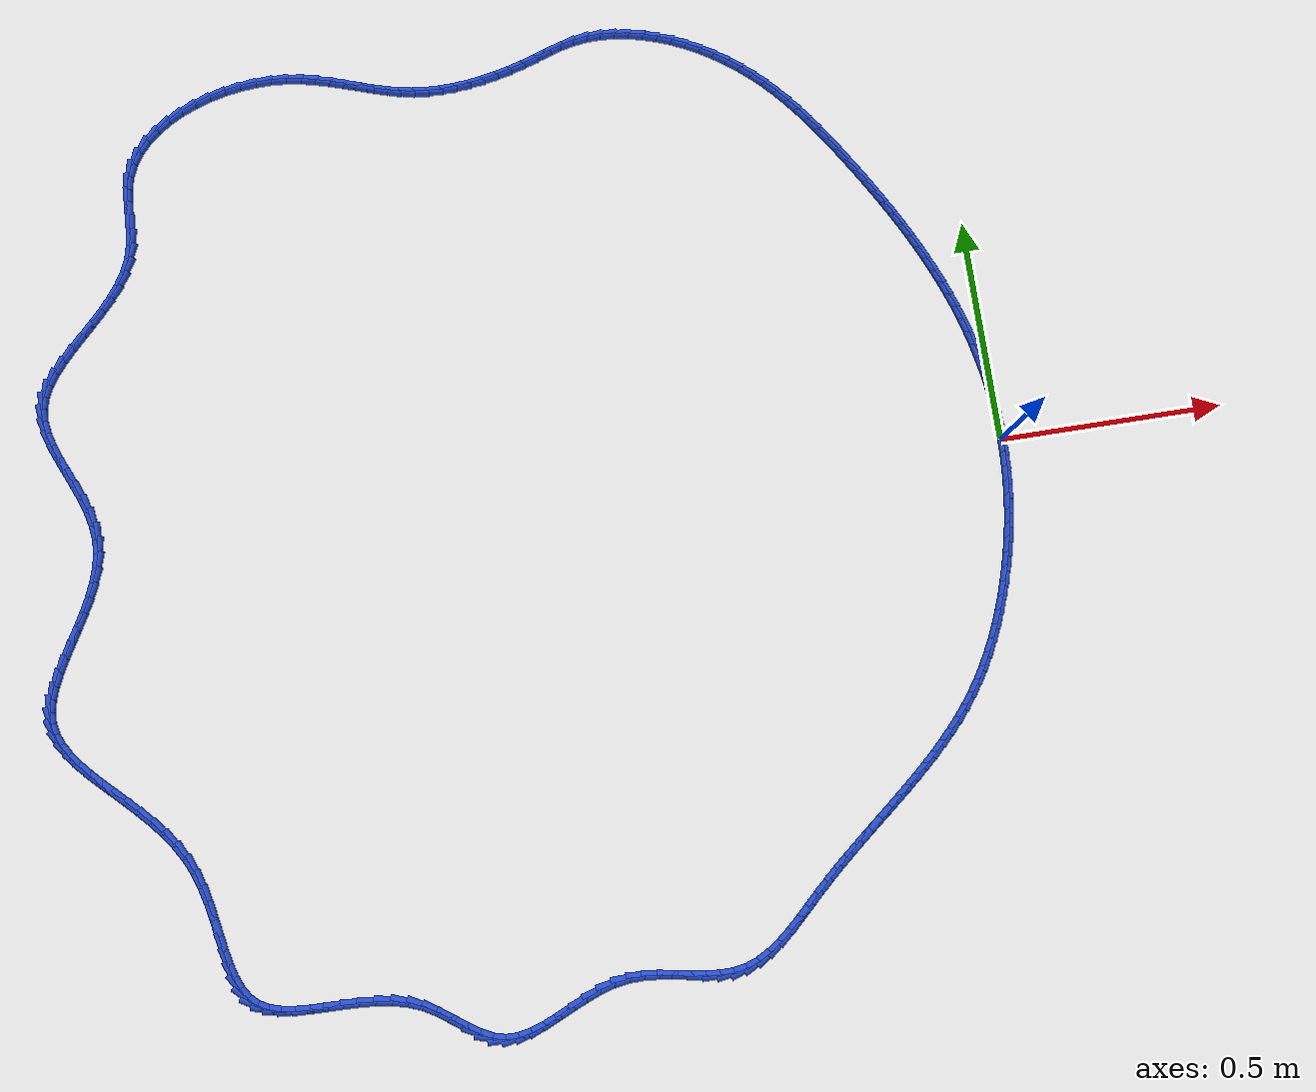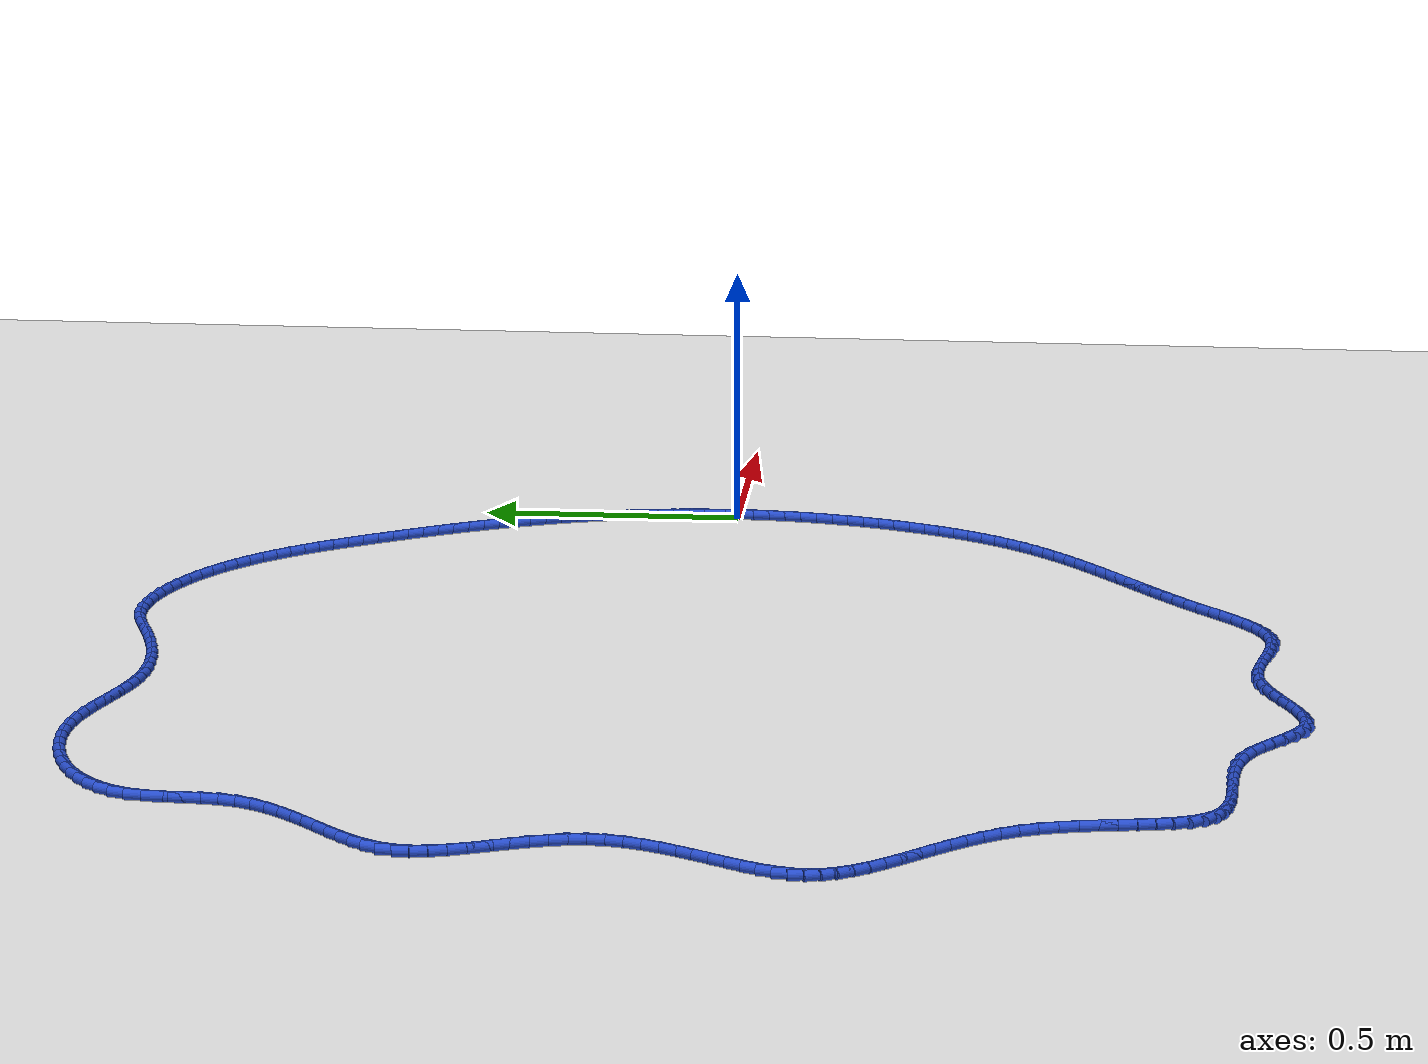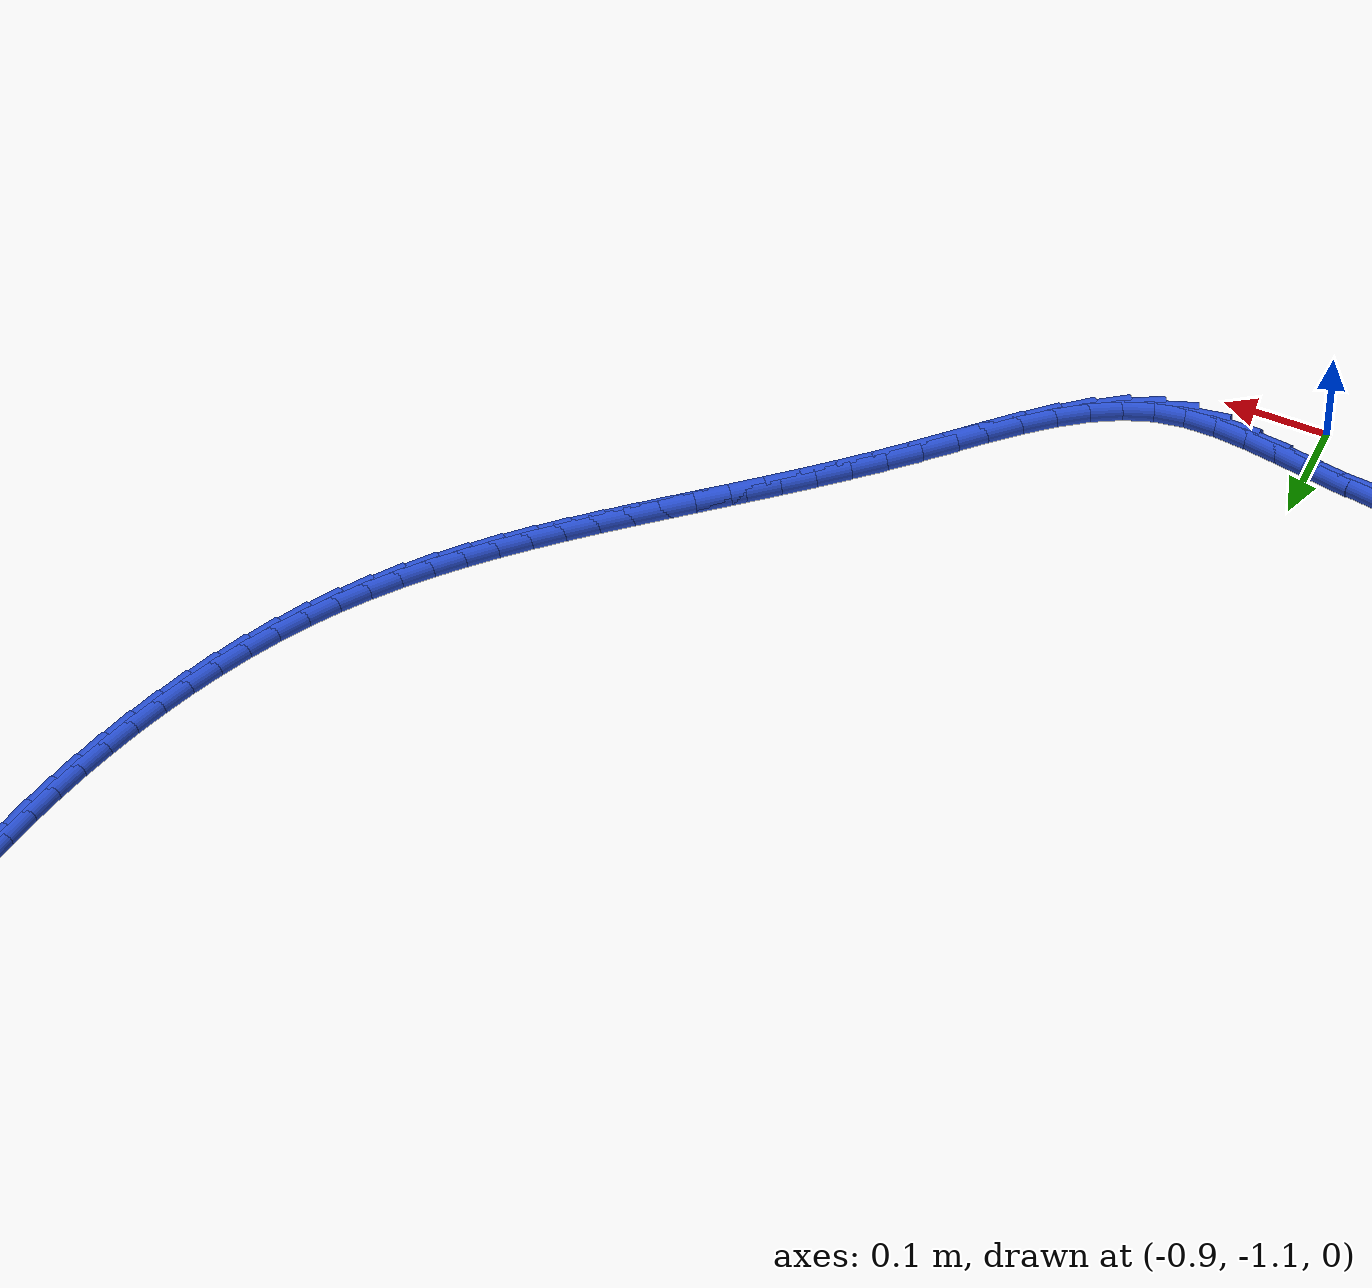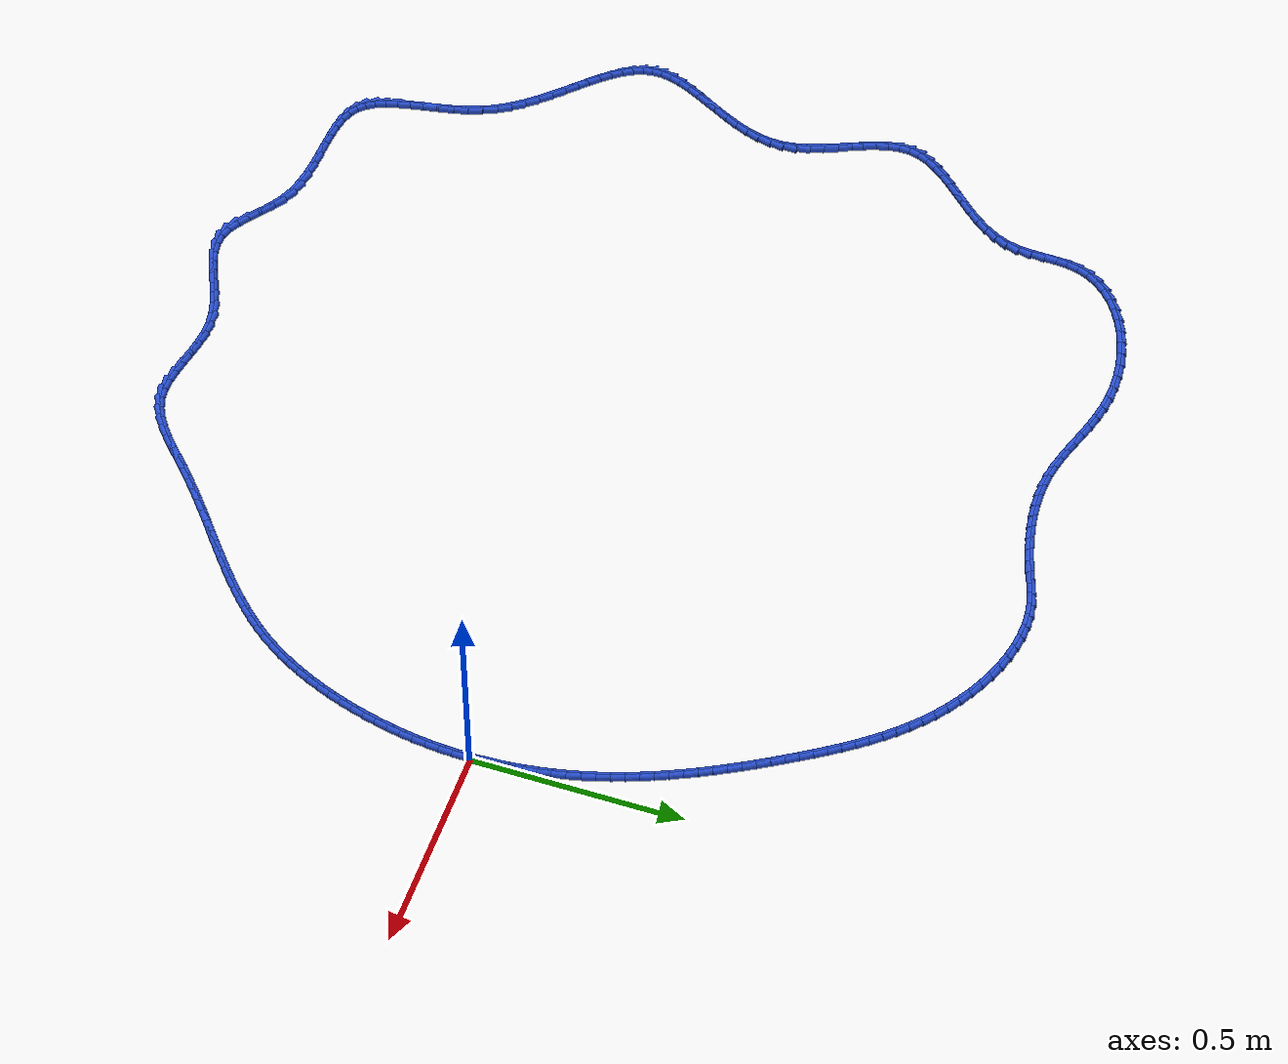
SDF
<sdf version="1.6">
 <world name="default">
  <light name="sun" type="directional">
   <pose>0 0 10 0 -0 0</pose>
   <diffuse>0.8 0.8 0.8 1</diffuse>
   <specular>0.2 0.2 0.2 1</specular>
   <attenuation>
    <range>1000</range>
    <constant>0.9</constant>
    <linear>0.01</linear>
    <quadratic>0.001</quadratic>
   </attenuation>
   <direction>-0.5 0.1 -0.9</direction>
  </light>
  <model name="ground_plane">
   <static>1</static>
   <link name="link">
    <collision name="collision">
     <geometry><plane><normal>0 0 1</normal><size>100 100</size></plane></geometry>
     <surface><friction><ode><mu>100</mu><mu2>50</mu2></ode></friction></surface>
    </collision>
    <visual name="visual">
     <cast_shadows>0</cast_shadows>
     <geometry><plane><normal>0 0 1</normal><size>100 100</size></plane></geometry>
     <material>
      <script><uri>file://media/materials/scripts/gazebo.material</uri><name>Gazebo/WhiteGlow</name></script>
     </material>
    </visual>
   </link>
  </model>
  <gravity>0 0 -9.8</gravity>
  <magnetic_field>6e-06 2.3e-05 -4.2e-05</magnetic_field>
  <atmosphere type="adiabatic"/>
  <physics name="default_physics" default="0" type="ode">
   <max_step_size>0.001</max_step_size>
   <real_time_factor>1</real_time_factor>
   <real_time_update_rate>1000</real_time_update_rate>
  </physics>
  <scene><ambient>0.4 0.4 0.4 1</ambient><background>0.7 0.7 0.7 1</background><shadows>1</shadows></scene>
  <spherical_coordinates>
   <surface_model>EARTH_WGS84</surface_model>
   <latitude_deg>0</latitude_deg>
   <longitude_deg>0</longitude_deg>
   <elevation>0</elevation>
   <heading_deg>0</heading_deg>
  </spherical_coordinates>
  <model name="line">
   <link name="link_0">
    <pose>3.209238430557093e-17 -1.3877787807814457e-17 0.01 0 1.57 -1.5539555337923852</pose>
    <collision name="collision">
     <geometry><cylinder><radius>0.01</radius><length>0.08</length></cylinder></geometry>
    </collision>
    <visual name="visual">
     <material>
      <script><name>Gazebo/Blue</name><uri>file://media/materials/scripts/gazebo.material</uri></script>
     </material>
     <geometry><cylinder><radius>0.01</radius><length>0.08</length></cylinder></geometry>
    </visual>
   </link>
   <link name="link_1">
    <pose>-0.0005427959826515752 0.03222797566954058 0.01 0 1.57 -1.520898807873776</pose>
    <collision name="collision">
     <geometry><cylinder><radius>0.01</radius><length>0.08</length></cylinder></geometry>
    </collision>
    <visual name="visual">
     <material>
      <script><name>Gazebo/Blue</name><uri>file://media/materials/scripts/gazebo.material</uri></script>
     </material>
     <geometry><cylinder><radius>0.01</radius><length>0.08</length></cylinder></geometry>
    </visual>
   </link>
   <link name="link_2">
    <pose>-0.002152261248135734 0.06445661849176589 0.01 0 1.57 -1.4883414030620206</pose>
    <collision name="collision">
     <geometry><cylinder><radius>0.01</radius><length>0.08</length></cylinder></geometry>
    </collision>
    <visual name="visual">
     <material>
      <script><name>Gazebo/Blue</name><uri>file://media/materials/scripts/gazebo.material</uri></script>
     </material>
     <geometry><cylinder><radius>0.01</radius><length>0.08</length></cylinder></geometry>
    </visual>
   </link>
   <link name="link_3">
    <pose>-0.004812398516318131 0.09664518674869334 0.01 0 1.57 -1.4562248974388412</pose>
    <collision name="collision">
     <geometry><cylinder><radius>0.01</radius><length>0.08</length></cylinder></geometry>
    </collision>
    <visual name="visual">
     <material>
      <script><name>Gazebo/Blue</name><uri>file://media/materials/scripts/gazebo.material</uri></script>
     </material>
     <geometry><cylinder><radius>0.01</radius><length>0.08</length></cylinder></geometry>
    </visual>
   </link>
   <link name="link_4">
    <pose>-0.008507210507064461 0.12875293872234053 0.01 0 1.57 -1.4244891618440185</pose>
    <collision name="collision">
     <geometry><cylinder><radius>0.01</radius><length>0.08</length></cylinder></geometry>
    </collision>
    <visual name="visual">
     <material>
      <script><name>Gazebo/Blue</name><uri>file://media/materials/scripts/gazebo.material</uri></script>
     </material>
     <geometry><cylinder><radius>0.01</radius><length>0.08</length></cylinder></geometry>
    </visual>
   </link>
   <link name="link_5">
    <pose>-0.013220699940240416 0.16073913269472495 0.01 0 1.57 -1.3930726529118578</pose>
    <collision name="collision">
     <geometry><cylinder><radius>0.01</radius><length>0.08</length></cylinder></geometry>
    </collision>
    <visual name="visual">
     <material>
      <script><name>Gazebo/Blue</name><uri>file://media/materials/scripts/gazebo.material</uri></script>
     </material>
     <geometry><cylinder><radius>0.01</radius><length>0.08</length></cylinder></geometry>
    </visual>
   </link>
   <link name="link_6">
    <pose>-0.018936869535711668 0.19256302694786406 0.01 0 1.57 -1.3619126327222981</pose>
    <collision name="collision">
     <geometry><cylinder><radius>0.01</radius><length>0.08</length></cylinder></geometry>
    </collision>
    <visual name="visual">
     <material>
      <script><name>Gazebo/Blue</name><uri>file://media/materials/scripts/gazebo.material</uri></script>
     </material>
     <geometry><cylinder><radius>0.01</radius><length>0.08</length></cylinder></geometry>
    </visual>
   </link>
   <link name="link_7">
    <pose>-0.02563972201334393 0.22418387976377552 0.01 0 1.57 -1.330945325788615</pose>
    <collision name="collision">
     <geometry><cylinder><radius>0.01</radius><length>0.08</length></cylinder></geometry>
    </collision>
    <visual name="visual">
     <material>
      <script><name>Gazebo/Blue</name><uri>file://media/materials/scripts/gazebo.material</uri></script>
     </material>
     <geometry><cylinder><radius>0.01</radius><length>0.08</length></cylinder></geometry>
    </visual>
   </link>
   <link name="link_8">
    <pose>-0.033313260093002874 0.25556094942447666 0.01 0 1.57 -1.3001069973551977</pose>
    <collision name="collision">
     <geometry><cylinder><radius>0.01</radius><length>0.08</length></cylinder></geometry>
    </collision>
    <visual name="visual">
     <material>
      <script><name>Gazebo/Blue</name><uri>file://media/materials/scripts/gazebo.material</uri></script>
     </material>
     <geometry><cylinder><radius>0.01</radius><length>0.08</length></cylinder></geometry>
    </visual>
   </link>
   <link name="link_9">
    <pose>-0.04194146313543204 0.2866535274796294 0.01 0 1.57 -1.2697153282985387</pose>
    <collision name="collision">
     <geometry><cylinder><radius>0.01</radius><length>0.08</length></cylinder></geometry>
    </collision>
    <visual name="visual">
     <material>
      <script><name>Gazebo/Blue</name><uri>file://media/materials/scripts/gazebo.material</uri></script>
     </material>
     <geometry><cylinder><radius>0.01</radius><length>0.08</length></cylinder></geometry>
    </visual>
   </link>
   <link name="link_10">
    <pose>-0.05149934680597828 0.31743367141365597 0.01 0 1.57 -1.2407146001281513</pose>
    <collision name="collision">
     <geometry><cylinder><radius>0.01</radius><length>0.08</length></cylinder></geometry>
    </collision>
    <visual name="visual">
     <material>
      <script><name>Gazebo/Blue</name><uri>file://media/materials/scripts/gazebo.material</uri></script>
     </material>
     <geometry><cylinder><radius>0.01</radius><length>0.08</length></cylinder></geometry>
    </visual>
   </link>
   <link name="link_11">
    <pose>-0.06193946427947058 0.3479054293884641 0.01 0 1.57 -1.2132811763538722</pose>
    <collision name="collision">
     <geometry><cylinder><radius>0.01</radius><length>0.08</length></cylinder></geometry>
    </collision>
    <visual name="visual">
     <material>
      <script><name>Gazebo/Blue</name><uri>file://media/materials/scripts/gazebo.material</uri></script>
     </material>
     <geometry><cylinder><radius>0.01</radius><length>0.08</length></cylinder></geometry>
    </visual>
   </link>
   <link name="link_12">
    <pose>-0.07321090688250925 0.37807777986832913 0.01 0 1.57 -1.1874345433328544</pose>
    <collision name="collision">
     <geometry><cylinder><radius>0.01</radius><length>0.08</length></cylinder></geometry>
    </collision>
    <visual name="visual">
     <material>
      <script><name>Gazebo/Blue</name><uri>file://media/materials/scripts/gazebo.material</uri></script>
     </material>
     <geometry><cylinder><radius>0.01</radius><length>0.08</length></cylinder></geometry>
    </visual>
   </link>
   <link name="link_13">
    <pose>-0.08526276594169455 0.40795970131752674 0.01 0 1.57 -1.1631834626038535</pose>
    <collision name="collision">
     <geometry><cylinder><radius>0.01</radius><length>0.08</length></cylinder></geometry>
    </collision>
    <visual name="visual">
     <material>
      <script><name>Gazebo/Blue</name><uri>file://media/materials/scripts/gazebo.material</uri></script>
     </material>
     <geometry><cylinder><radius>0.01</radius><length>0.08</length></cylinder></geometry>
    </visual>
   </link>
   <link name="link_14">
    <pose>-0.09804413278362671 0.43756017220033244 0.01 0 1.57 -1.1405279082285322</pose>
    <collision name="collision">
     <geometry><cylinder><radius>0.01</radius><length>0.08</length></cylinder></geometry>
    </collision>
    <visual name="visual">
     <material>
      <script><name>Gazebo/Blue</name><uri>file://media/materials/scripts/gazebo.material</uri></script>
     </material>
     <geometry><cylinder><radius>0.01</radius><length>0.08</length></cylinder></geometry>
    </visual>
   </link>
   <link name="link_15">
    <pose>-0.11150409873490603 0.4668881709810217 0.01 0 1.57 -1.119460937089077</pose>
    <collision name="collision">
     <geometry><cylinder><radius>0.01</radius><length>0.08</length></cylinder></geometry>
    </collision>
    <visual name="visual">
     <material>
      <script><name>Gazebo/Blue</name><uri>file://media/materials/scripts/gazebo.material</uri></script>
     </material>
     <geometry><cylinder><radius>0.01</radius><length>0.08</length></cylinder></geometry>
    </visual>
   </link>
   <link name="link_16">
    <pose>-0.12559175512213278 0.4959526761238701 0.01 0 1.57 -1.0999704429787138</pose>
    <collision name="collision">
     <geometry><cylinder><radius>0.01</radius><length>0.08</length></cylinder></geometry>
    </collision>
    <visual name="visual">
     <material>
      <script><name>Gazebo/Blue</name><uri>file://media/materials/scripts/gazebo.material</uri></script>
     </material>
     <geometry><cylinder><radius>0.01</radius><length>0.08</length></cylinder></geometry>
    </visual>
   </link>
   <link name="link_17">
    <pose>-0.1402561932719072 0.5247626660931531 0.01 0 1.57 -1.0820407642688685</pose>
    <collision name="collision">
     <geometry><cylinder><radius>0.01</radius><length>0.08</length></cylinder></geometry>
    </collision>
    <visual name="visual">
     <material>
      <script><name>Gazebo/Blue</name><uri>file://media/materials/scripts/gazebo.material</uri></script>
     </material>
     <geometry><cylinder><radius>0.01</radius><length>0.08</length></cylinder></geometry>
    </visual>
   </link>
   <link name="link_18">
    <pose>-0.15544650451082953 0.5533271193531463 0.01 0 1.57 -1.0656541305282947</pose>
    <collision name="collision">
     <geometry><cylinder><radius>0.01</radius><length>0.08</length></cylinder></geometry>
    </collision>
    <visual name="visual">
     <material>
      <script><name>Gazebo/Blue</name><uri>file://media/materials/scripts/gazebo.material</uri></script>
     </material>
     <geometry><cylinder><radius>0.01</radius><length>0.08</length></cylinder></geometry>
    </visual>
   </link>
   <link name="link_19">
    <pose>-0.17111178016550005 0.581655014368125 0.01 0 1.57 -1.0507919455268815</pose>
    <collision name="collision">
     <geometry><cylinder><radius>0.01</radius><length>0.08</length></cylinder></geometry>
    </collision>
    <visual name="visual">
     <material>
      <script><name>Gazebo/Blue</name><uri>file://media/materials/scripts/gazebo.material</uri></script>
     </material>
     <geometry><cylinder><radius>0.01</radius><length>0.08</length></cylinder></geometry>
    </visual>
   </link>
   <link name="link_20">
    <pose>-0.18720111156251906 0.609755329602365 0.01 0 1.57 -1.0374359127916968</pose>
    <collision name="collision">
     <geometry><cylinder><radius>0.01</radius><length>0.08</length></cylinder></geometry>
    </collision>
    <visual name="visual">
     <material>
      <script><name>Gazebo/Blue</name><uri>file://media/materials/scripts/gazebo.material</uri></script>
     </material>
     <geometry><cylinder><radius>0.01</radius><length>0.08</length></cylinder></geometry>
    </visual>
   </link>
   <link name="link_21">
    <pose>-0.20366359002848672 0.6376370435201415 0.01 0 1.57 -1.0255690157267685</pose>
    <collision name="collision">
     <geometry><cylinder><radius>0.01</radius><length>0.08</length></cylinder></geometry>
    </collision>
    <visual name="visual">
     <material>
      <script><name>Gazebo/Blue</name><uri>file://media/materials/scripts/gazebo.material</uri></script>
     </material>
     <geometry><cylinder><radius>0.01</radius><length>0.08</length></cylinder></geometry>
    </visual>
   </link>
   <link name="link_22">
    <pose>-0.2204483068900034 0.6653091345857304 0.01 0 1.57 -1.0151669082482915</pose>
    <collision name="collision">
     <geometry><cylinder><radius>0.01</radius><length>0.08</length></cylinder></geometry>
    </collision>
    <visual name="visual">
     <material>
      <script><name>Gazebo/Blue</name><uri>file://media/materials/scripts/gazebo.material</uri></script>
     </material>
     <geometry><cylinder><radius>0.01</radius><length>0.08</length></cylinder></geometry>
    </visual>
   </link>
   <link name="link_23">
    <pose>-0.23750461993949099 0.6927804305493603 0.01 0 1.57 -1.004461871084795</pose>
    <collision name="collision">
     <geometry><cylinder><radius>0.01</radius><length>0.08</length></cylinder></geometry>
    </collision>
    <visual name="visual">
     <material>
      <script><name>Gazebo/Blue</name><uri>file://media/materials/scripts/gazebo.material</uri></script>
     </material>
     <geometry><cylinder><radius>0.01</radius><length>0.08</length></cylinder></geometry>
    </visual>
   </link>
   <link name="link_24">
    <pose>-0.2548312977966818 0.7200318122159919 0.01 0 1.57 -0.9896352712538162</pose>
    <collision name="collision">
     <geometry><cylinder><radius>0.01</radius><length>0.08</length></cylinder></geometry>
    </collision>
    <visual name="visual">
     <material>
      <script><name>Gazebo/Blue</name><uri>file://media/materials/scripts/gazebo.material</uri></script>
     </material>
     <geometry><cylinder><radius>0.01</radius><length>0.08</length></cylinder></geometry>
    </visual>
   </link>
   <link name="link_25">
    <pose>-0.2725340618901679 0.7469836674893697 0.01 0 1.57 -0.9701662959529438</pose>
    <collision name="collision">
     <geometry><cylinder><radius>0.01</radius><length>0.08</length></cylinder></geometry>
    </collision>
    <visual name="visual">
     <material>
      <script><name>Gazebo/Blue</name><uri>file://media/materials/scripts/gazebo.material</uri></script>
     </material>
     <geometry><cylinder><radius>0.01</radius><length>0.08</length></cylinder></geometry>
    </visual>
   </link>
   <link name="link_26">
    <pose>-0.29073260863809547 0.773548479967857 0.01 0 1.57 -0.9460405259507334</pose>
    <collision name="collision">
     <geometry><cylinder><radius>0.01</radius><length>0.08</length></cylinder></geometry>
    </collision>
    <visual name="visual">
     <material>
      <script><name>Gazebo/Blue</name><uri>file://media/materials/scripts/gazebo.material</uri></script>
     </material>
     <geometry><cylinder><radius>0.01</radius><length>0.08</length></cylinder></geometry>
    </visual>
   </link>
   <link name="link_27">
    <pose>-0.3095466344586112 0.799638733249817 0.01 0 1.57 -0.9172665106980608</pose>
    <collision name="collision">
     <geometry><cylinder><radius>0.01</radius><length>0.08</length></cylinder></geometry>
    </collision>
    <visual name="visual">
     <material>
      <script><name>Gazebo/Blue</name><uri>file://media/materials/scripts/gazebo.material</uri></script>
     </material>
     <geometry><cylinder><radius>0.01</radius><length>0.08</length></cylinder></geometry>
    </visual>
   </link>
   <link name="link_28">
    <pose>-0.3290958357698615 0.825166910933613 0.01 0 1.57 -0.8838913671172155</pose>
    <collision name="collision">
     <geometry><cylinder><radius>0.01</radius><length>0.08</length></cylinder></geometry>
    </collision>
    <visual name="visual">
     <material>
      <script><name>Gazebo/Blue</name><uri>file://media/materials/scripts/gazebo.material</uri></script>
     </material>
     <geometry><cylinder><radius>0.01</radius><length>0.08</length></cylinder></geometry>
    </visual>
   </link>
   <link name="link_29">
    <pose>-0.34949990898999295 0.8500454966176083 0.01 0 1.57 -0.8460186242015016</pose>
    <collision name="collision">
     <geometry><cylinder><radius>0.01</radius><length>0.08</length></cylinder></geometry>
    </collision>
    <visual name="visual">
     <material>
      <script><name>Gazebo/Blue</name><uri>file://media/materials/scripts/gazebo.material</uri></script>
     </material>
     <geometry><cylinder><radius>0.01</radius><length>0.08</length></cylinder></geometry>
    </visual>
   </link>
   <link name="link_30">
    <pose>-0.3708785505371519 0.8741869739001658 0.01 0 1.57 -0.8038269707775569</pose>
    <collision name="collision">
     <geometry><cylinder><radius>0.01</radius><length>0.08</length></cylinder></geometry>
    </collision>
    <visual name="visual">
     <material>
      <script><name>Gazebo/Blue</name><uri>file://media/materials/scripts/gazebo.material</uri></script>
     </material>
     <geometry><cylinder><radius>0.01</radius><length>0.08</length></cylinder></geometry>
    </visual>
   </link>
   <link name="link_31">
    <pose>-0.393351456829485 0.8975038263796491 0.01 0 1.57 -0.7575877552655206</pose>
    <collision name="collision">
     <geometry><cylinder><radius>0.01</radius><length>0.08</length></cylinder></geometry>
    </collision>
    <visual name="visual">
     <material>
      <script><name>Gazebo/Blue</name><uri>file://media/materials/scripts/gazebo.material</uri></script>
     </material>
     <geometry><cylinder><radius>0.01</radius><length>0.08</length></cylinder></geometry>
    </visual>
   </link>
   <link name="link_32">
    <pose>-0.4170383242851389 0.9199085376544217 0.01 0 1.57 -0.7076783172298815</pose>
    <collision name="collision">
     <geometry><cylinder><radius>0.01</radius><length>0.08</length></cylinder></geometry>
    </collision>
    <visual name="visual">
     <material>
      <script><name>Gazebo/Blue</name><uri>file://media/materials/scripts/gazebo.material</uri></script>
     </material>
     <geometry><cylinder><radius>0.01</radius><length>0.08</length></cylinder></geometry>
    </visual>
   </link>
   <link name="link_33">
    <pose>-0.4420588493222596 0.9413135913228461 0.01 0 1.57 -0.6547674667389537</pose>
    <collision name="collision">
     <geometry><cylinder><radius>0.01</radius><length>0.08</length></cylinder></geometry>
    </collision>
    <visual name="visual">
     <material>
      <script><name>Gazebo/Blue</name><uri>file://media/materials/scripts/gazebo.material</uri></script>
     </material>
     <geometry><cylinder><radius>0.01</radius><length>0.08</length></cylinder></geometry>
    </visual>
   </link>
   <link name="link_34">
    <pose>-0.4685146378490364 0.9616251408655392 0.01 0 1.57 -0.6008056684630555</pose>
    <collision name="collision">
     <geometry><cylinder><radius>0.01</radius><length>0.08</length></cylinder></geometry>
    </collision>
    <visual name="visual">
     <material>
      <script><name>Gazebo/Blue</name><uri>file://media/materials/scripts/gazebo.material</uri></script>
     </material>
     <geometry><cylinder><radius>0.01</radius><length>0.08</length></cylinder></geometry>
    </visual>
   </link>
   <link name="link_35">
    <pose>-0.496329196940261 0.9806870205367018 0.01 0 1.57 -0.5460620051062839</pose>
    <collision name="collision">
     <geometry><cylinder><radius>0.01</radius><length>0.08</length></cylinder></geometry>
    </collision>
    <visual name="visual">
     <material>
      <script><name>Gazebo/Blue</name><uri>file://media/materials/scripts/gazebo.material</uri></script>
     </material>
     <geometry><cylinder><radius>0.01</radius><length>0.08</length></cylinder></geometry>
    </visual>
   </link>
   <link name="link_36">
    <pose>-0.5253247778276172 0.9983076337811789 0.01 0 1.57 -0.4896607806850039</pose>
    <collision name="collision">
     <geometry><cylinder><radius>0.01</radius><length>0.08</length></cylinder></geometry>
    </collision>
    <visual name="visual">
     <material>
      <script><name>Gazebo/Blue</name><uri>file://media/materials/scripts/gazebo.material</uri></script>
     </material>
     <geometry><cylinder><radius>0.01</radius><length>0.08</length></cylinder></geometry>
    </visual>
   </link>
   <link name="link_37">
    <pose>-0.555322463433089 1.0142949752362165 0.01 0 1.57 -0.4307225839419919</pose>
    <collision name="collision">
     <geometry><cylinder><radius>0.01</radius><length>0.08</length></cylinder></geometry>
    </collision>
    <visual name="visual">
     <material>
      <script><name>Gazebo/Blue</name><uri>file://media/materials/scripts/gazebo.material</uri></script>
     </material>
     <geometry><cylinder><radius>0.01</radius><length>0.08</length></cylinder></geometry>
    </visual>
   </link>
   <link name="link_38">
    <pose>-0.5861433366786596 1.028457039539059 0.01 0 1.57 -0.368358334791129</pose>
    <collision name="collision">
     <geometry><cylinder><radius>0.01</radius><length>0.08</length></cylinder></geometry>
    </collision>
    <visual name="visual">
     <material>
      <script><name>Gazebo/Blue</name><uri>file://media/materials/scripts/gazebo.material</uri></script>
     </material>
     <geometry><cylinder><radius>0.01</radius><length>0.08</length></cylinder></geometry>
    </visual>
   </link>
   <link name="link_39">
    <pose>-0.6176084804863127 1.0406018213269521 0.01 0 1.57 -0.30166363081155684</pose>
    <collision name="collision">
     <geometry><cylinder><radius>0.01</radius><length>0.08</length></cylinder></geometry>
    </collision>
    <visual name="visual">
     <material>
      <script><name>Gazebo/Blue</name><uri>file://media/materials/scripts/gazebo.material</uri></script>
     </material>
     <geometry><cylinder><radius>0.01</radius><length>0.08</length></cylinder></geometry>
    </visual>
   </link>
   <link name="link_40">
    <pose>-0.6495389777780314 1.0505373152371402 0.01 0 1.57 -0.22972983413771358</pose>
    <collision name="collision">
     <geometry><cylinder><radius>0.01</radius><length>0.08</length></cylinder></geometry>
    </collision>
    <visual name="visual">
     <material>
      <script><name>Gazebo/Blue</name><uri>file://media/materials/scripts/gazebo.material</uri></script>
     </material>
     <geometry><cylinder><radius>0.01</radius><length>0.08</length></cylinder></geometry>
    </visual>
   </link>
   <link name="link_41">
    <pose>-0.6817559114757996 1.058071515906868 0.01 0 1.57 -0.1516793694242874</pose>
    <collision name="collision">
     <geometry><cylinder><radius>0.01</radius><length>0.08</length></cylinder></geometry>
    </collision>
    <visual name="visual">
     <material>
      <script><name>Gazebo/Blue</name><uri>file://media/materials/scripts/gazebo.material</uri></script>
     </material>
     <geometry><cylinder><radius>0.01</radius><length>0.08</length></cylinder></geometry>
    </visual>
   </link>
   <link name="link_42">
    <pose>-0.7140803645016007 1.0630124179733818 0.01 0 1.57 -0.06673467472127449</pose>
    <collision name="collision">
     <geometry><cylinder><radius>0.01</radius><length>0.08</length></cylinder></geometry>
    </collision>
    <visual name="visual">
     <material>
      <script><name>Gazebo/Blue</name><uri>file://media/materials/scripts/gazebo.material</uri></script>
     </material>
     <geometry><cylinder><radius>0.01</radius><length>0.08</length></cylinder></geometry>
    </visual>
   </link>
   <link name="link_43">
    <pose>-0.7463334197774187 1.0651680160739256 0.01 0 1.57 0.025670636677717056</pose>
    <collision name="collision">
     <geometry><cylinder><radius>0.01</radius><length>0.08</length></cylinder></geometry>
    </collision>
    <visual name="visual">
     <material>
      <script><name>Gazebo/Blue</name><uri>file://media/materials/scripts/gazebo.material</uri></script>
     </material>
     <geometry><cylinder><radius>0.01</radius><length>0.08</length></cylinder></geometry>
    </visual>
   </link>
   <link name="link_44">
    <pose>-0.7783361602252366 1.064346304845745 0.01 0 1.57 0.12573740877094772</pose>
    <collision name="collision">
     <geometry><cylinder><radius>0.01</radius><length>0.08</length></cylinder></geometry>
    </collision>
    <visual name="visual">
     <material>
      <script><name>Gazebo/Blue</name><uri>file://media/materials/scripts/gazebo.material</uri></script>
     </material>
     <geometry><cylinder><radius>0.01</radius><length>0.08</length></cylinder></geometry>
    </visual>
   </link>
   <link name="link_45">
    <pose>-0.8099096687670382 1.0603552789260853 0.01 0 1.57 0.22784267795476293</pose>
    <collision name="collision">
     <geometry><cylinder><radius>0.01</radius><length>0.08</length></cylinder></geometry>
    </collision>
    <visual name="visual">
     <material>
      <script><name>Gazebo/Blue</name><uri>file://media/materials/scripts/gazebo.material</uri></script>
     </material>
     <geometry><cylinder><radius>0.01</radius><length>0.08</length></cylinder></geometry>
    </visual>
   </link>
   <link name="link_46">
    <pose>-0.8409326739852288 1.0531620083803703 0.01 0 1.57 0.2969438872481152</pose>
    <collision name="collision">
     <geometry><cylinder><radius>0.01</radius><length>0.08</length></cylinder></geometry>
    </collision>
    <visual name="visual">
     <material>
      <script><name>Gazebo/Blue</name><uri>file://media/materials/scripts/gazebo.material</uri></script>
     </material>
     <geometry><cylinder><radius>0.01</radius><length>0.08</length></cylinder></geometry>
    </visual>
   </link>
   <link name="link_47">
    <pose>-0.8716561880112182 1.0437608941178123 0.01 0 1.57 0.31976469669557983</pose>
    <collision name="collision">
     <geometry><cylinder><radius>0.01</radius><length>0.08</length></cylinder></geometry>
    </collision>
    <visual name="visual">
     <material>
      <script><name>Gazebo/Blue</name><uri>file://media/materials/scripts/gazebo.material</uri></script>
     </material>
     <geometry><cylinder><radius>0.01</radius><length>0.08</length></cylinder></geometry>
    </visual>
   </link>
   <link name="link_48">
    <pose>-0.9024791475073302 1.033554540508576 0.01 0 1.57 0.30025945216626276</pose>
    <collision name="collision">
     <geometry><cylinder><radius>0.01</radius><length>0.08</length></cylinder></geometry>
    </collision>
    <visual name="visual">
     <material>
      <script><name>Gazebo/Blue</name><uri>file://media/materials/scripts/gazebo.material</uri></script>
     </material>
     <geometry><cylinder><radius>0.01</radius><length>0.08</length></cylinder></geometry>
    </visual>
   </link>
   <link name="link_49">
    <pose>-0.9337665579952034 1.023867315224693 0.01 0 1.57 0.26400829053002695</pose>
    <collision name="collision">
     <geometry><cylinder><radius>0.01</radius><length>0.08</length></cylinder></geometry>
    </collision>
    <visual name="visual">
     <material>
      <script><name>Gazebo/Blue</name><uri>file://media/materials/scripts/gazebo.material</uri></script>
     </material>
     <geometry><cylinder><radius>0.01</radius><length>0.08</length></cylinder></geometry>
    </visual>
   </link>
   <link name="link_50">
    <pose>-0.9655587339250417 1.0152733148491182 0.01 0 1.57 0.22440531076914905</pose>
    <collision name="collision">
     <geometry><cylinder><radius>0.01</radius><length>0.08</length></cylinder></geometry>
    </collision>
    <visual name="visual">
     <material>
      <script><name>Gazebo/Blue</name><uri>file://media/materials/scripts/gazebo.material</uri></script>
     </material>
     <geometry><cylinder><radius>0.01</radius><length>0.08</length></cylinder></geometry>
    </visual>
   </link>
   <link name="link_51">
    <pose>-0.9977170641098532 1.0079331884003615 0.01 0 1.57 0.18110619935295755</pose>
    <collision name="collision">
     <geometry><cylinder><radius>0.01</radius><length>0.08</length></cylinder></geometry>
    </collision>
    <visual name="visual">
     <material>
      <script><name>Gazebo/Blue</name><uri>file://media/materials/scripts/gazebo.material</uri></script>
     </material>
     <geometry><cylinder><radius>0.01</radius><length>0.08</length></cylinder></geometry>
    </visual>
   </link>
   <link name="link_52">
    <pose>-1.0301010697268254 1.0020032693081022 0.01 0 1.57 0.1335848246292097</pose>
    <collision name="collision">
     <geometry><cylinder><radius>0.01</radius><length>0.08</length></cylinder></geometry>
    </collision>
    <visual name="visual">
     <material>
      <script><name>Gazebo/Blue</name><uri>file://media/materials/scripts/gazebo.material</uri></script>
     </material>
     <geometry><cylinder><radius>0.01</radius><length>0.08</length></cylinder></geometry>
    </visual>
   </link>
   <link name="link_53">
    <pose>-1.0625702719531458 0.9976398910020214 0.01 0 1.57 0.081282559596008</pose>
    <collision name="collision">
     <geometry><cylinder><radius>0.01</radius><length>0.08</length></cylinder></geometry>
    </collision>
    <visual name="visual">
     <material>
      <script><name>Gazebo/Blue</name><uri>file://media/materials/scripts/gazebo.material</uri></script>
     </material>
     <geometry><cylinder><radius>0.01</radius><length>0.08</length></cylinder></geometry>
    </visual>
   </link>
   <link name="link_54">
    <pose>-1.0949841919660024 0.9949993869117982 0.01 0 1.57 0.023625024721228384</pose>
    <collision name="collision">
     <geometry><cylinder><radius>0.01</radius><length>0.08</length></cylinder></geometry>
    </collision>
    <visual name="visual">
     <material>
      <script><name>Gazebo/Blue</name><uri>file://media/materials/scripts/gazebo.material</uri></script>
     </material>
     <geometry><cylinder><radius>0.01</radius><length>0.08</length></cylinder></geometry>
    </visual>
   </link>
   <link name="link_55">
    <pose>-1.1272023509425824 0.9942380904671126 0.01 0 1.57 -0.03994636514419881</pose>
    <collision name="collision">
     <geometry><cylinder><radius>0.01</radius><length>0.08</length></cylinder></geometry>
    </collision>
    <visual name="visual">
     <material>
      <script><name>Gazebo/Blue</name><uri>file://media/materials/scripts/gazebo.material</uri></script>
     </material>
     <geometry><cylinder><radius>0.01</radius><length>0.08</length></cylinder></geometry>
    </visual>
   </link>
   <link name="link_56">
    <pose>-1.159084270060073 0.9955123350976445 0.01 0 1.57 -0.10992279723840942</pose>
    <collision name="collision">
     <geometry><cylinder><radius>0.01</radius><length>0.08</length></cylinder></geometry>
    </collision>
    <visual name="visual">
     <material>
      <script><name>Gazebo/Blue</name><uri>file://media/materials/scripts/gazebo.material</uri></script>
     </material>
     <geometry><cylinder><radius>0.01</radius><length>0.08</length></cylinder></geometry>
    </visual>
   </link>
   <link name="link_57">
    <pose>-1.190489470495663 0.9989784542330741 0.01 0 1.57 -0.184534241785324</pose>
    <collision name="collision">
     <geometry><cylinder><radius>0.01</radius><length>0.08</length></cylinder></geometry>
    </collision>
    <visual name="visual">
     <material>
      <script><name>Gazebo/Blue</name><uri>file://media/materials/scripts/gazebo.material</uri></script>
     </material>
     <geometry><cylinder><radius>0.01</radius><length>0.08</length></cylinder></geometry>
    </visual>
   </link>
   <link name="link_58">
    <pose>-1.2213084531121094 1.004731058132297 0.01 0 1.57 -0.2476584669770083</pose>
    <collision name="collision">
     <geometry><cylinder><radius>0.01</radius><length>0.08</length></cylinder></geometry>
    </collision>
    <visual name="visual">
     <material>
      <script><name>Gazebo/Blue</name><uri>file://media/materials/scripts/gazebo.material</uri></script>
     </material>
     <geometry><cylinder><radius>0.01</radius><length>0.08</length></cylinder></geometry>
    </visual>
   </link>
   <link name="link_59">
    <pose>-1.2516620097746585 1.012405930871346 0.01 0 1.57 -0.29122634679704756</pose>
    <collision name="collision">
     <geometry><cylinder><radius>0.01</radius><length>0.08</length></cylinder></geometry>
    </collision>
    <visual name="visual">
     <material>
      <script><name>Gazebo/Blue</name><uri>file://media/materials/scripts/gazebo.material</uri></script>
     </material>
     <geometry><cylinder><radius>0.01</radius><length>0.08</length></cylinder></geometry>
    </visual>
   </link>
   <link name="link_60">
    <pose>-1.2817746728939043 1.0214321663910941 0.01 0 1.57 -0.31496000012980724</pose>
    <collision name="collision">
     <geometry><cylinder><radius>0.01</radius><length>0.08</length></cylinder></geometry>
    </collision>
    <visual name="visual">
     <material>
      <script><name>Gazebo/Blue</name><uri>file://media/materials/scripts/gazebo.material</uri></script>
     </material>
     <geometry><cylinder><radius>0.01</radius><length>0.08</length></cylinder></geometry>
    </visual>
   </link>
   <link name="link_61">
    <pose>-1.3118714755453014 1.031237861119946 0.01 0 1.57 -0.319112880362789</pose>
    <collision name="collision">
     <geometry><cylinder><radius>0.01</radius><length>0.08</length></cylinder></geometry>
    </collision>
    <visual name="visual">
     <material>
      <script><name>Gazebo/Blue</name><uri>file://media/materials/scripts/gazebo.material</uri></script>
     </material>
     <geometry><cylinder><radius>0.01</radius><length>0.08</length></cylinder></geometry>
    </visual>
   </link>
   <link name="link_62">
    <pose>-1.3421774508043023 1.0412511114863054 0.01 0 1.57 -0.3041467638296031</pose>
    <collision name="collision">
     <geometry><cylinder><radius>0.01</radius><length>0.08</length></cylinder></geometry>
    </collision>
    <visual name="visual">
     <material>
      <script><name>Gazebo/Blue</name><uri>file://media/materials/scripts/gazebo.material</uri></script>
     </material>
     <geometry><cylinder><radius>0.01</radius><length>0.08</length></cylinder></geometry>
    </visual>
   </link>
   <link name="link_63">
    <pose>-1.3729176317463616 1.050900013918577 0.01 0 1.57 -0.2706686063330813</pose>
    <collision name="collision">
     <geometry><cylinder><radius>0.01</radius><length>0.08</length></cylinder></geometry>
    </collision>
    <visual name="visual">
     <material>
      <script><name>Gazebo/Blue</name><uri>file://media/materials/scripts/gazebo.material</uri></script>
     </material>
     <geometry><cylinder><radius>0.01</radius><length>0.08</length></cylinder></geometry>
    </visual>
   </link>
   <link name="link_64">
    <pose>-1.404317051446933 1.0596126648451647 0.01 0 1.57 -0.21956439943451625</pose>
    <collision name="collision">
     <geometry><cylinder><radius>0.01</radius><length>0.08</length></cylinder></geometry>
    </collision>
    <visual name="visual">
     <material>
      <script><name>Gazebo/Blue</name><uri>file://media/materials/scripts/gazebo.material</uri></script>
     </material>
     <geometry><cylinder><radius>0.01</radius><length>0.08</length></cylinder></geometry>
    </visual>
   </link>
   <link name="link_65">
    <pose>-1.4366007429814707 1.0668171606944739 0.01 0 1.57 -0.1522705587111267</pose>
    <collision name="collision">
     <geometry><cylinder><radius>0.01</radius><length>0.08</length></cylinder></geometry>
    </collision>
    <visual name="visual">
     <material>
      <script><name>Gazebo/Blue</name><uri>file://media/materials/scripts/gazebo.material</uri></script>
     </material>
     <geometry><cylinder><radius>0.01</radius><length>0.08</length></cylinder></geometry>
    </visual>
   </link>
   <link name="link_66">
    <pose>-1.469993739425428 1.071941597894908 0.01 0 1.57 -0.07186552564823748</pose>
    <collision name="collision">
     <geometry><cylinder><radius>0.01</radius><length>0.08</length></cylinder></geometry>
    </collision>
    <visual name="visual">
     <material>
      <script><name>Gazebo/Blue</name><uri>file://media/materials/scripts/gazebo.material</uri></script>
     </material>
     <geometry><cylinder><radius>0.01</radius><length>0.08</length></cylinder></geometry>
    </visual>
   </link>
   <link name="link_67">
    <pose>-1.5046902370949278 1.0744393814818423 0.01 0 1.57 0.009241513793314183</pose>
    <collision name="collision">
     <geometry><cylinder><radius>0.01</radius><length>0.08</length></cylinder></geometry>
    </collision>
    <visual name="visual">
     <material>
      <script><name>Gazebo/Blue</name><uri>file://media/materials/scripts/gazebo.material</uri></script>
     </material>
     <geometry><cylinder><radius>0.01</radius><length>0.08</length></cylinder></geometry>
    </visual>
   </link>
   <link name="link_68">
    <pose>-1.5404642574492529 1.0741087659671056 0.01 0 1.57 0.08545857403335835</pose>
    <collision name="collision">
     <geometry><cylinder><radius>0.01</radius><length>0.08</length></cylinder></geometry>
    </collision>
    <visual name="visual">
     <material>
      <script><name>Gazebo/Blue</name><uri>file://media/materials/scripts/gazebo.material</uri></script>
     </material>
     <geometry><cylinder><radius>0.01</radius><length>0.08</length></cylinder></geometry>
    </visual>
   </link>
   <link name="link_69">
    <pose>-1.5767862422158772 1.070997162397883 0.01 0 1.57 0.15935996623190674</pose>
    <collision name="collision">
     <geometry><cylinder><radius>0.01</radius><length>0.08</length></cylinder></geometry>
    </collision>
    <visual name="visual">
     <material>
      <script><name>Gazebo/Blue</name><uri>file://media/materials/scripts/gazebo.material</uri></script>
     </material>
     <geometry><cylinder><radius>0.01</radius><length>0.08</length></cylinder></geometry>
    </visual>
   </link>
   <link name="link_70">
    <pose>-1.6131198903788633 1.0651575157829942 0.01 0 1.57 0.23344689845944122</pose>
    <collision name="collision">
     <geometry><cylinder><radius>0.01</radius><length>0.08</length></cylinder></geometry>
    </collision>
    <visual name="visual">
     <material>
      <script><name>Gazebo/Blue</name><uri>file://media/materials/scripts/gazebo.material</uri></script>
     </material>
     <geometry><cylinder><radius>0.01</radius><length>0.08</length></cylinder></geometry>
    </visual>
   </link>
   <link name="link_71">
    <pose>-1.6489289009222703 1.0566427711312594 0.01 0 1.57 0.31016010478622685</pose>
    <collision name="collision">
     <geometry><cylinder><radius>0.01</radius><length>0.08</length></cylinder></geometry>
    </collision>
    <visual name="visual">
     <material>
      <script><name>Gazebo/Blue</name><uri>file://media/materials/scripts/gazebo.material</uri></script>
     </material>
     <geometry><cylinder><radius>0.01</radius><length>0.08</length></cylinder></geometry>
    </visual>
   </link>
   <link name="link_72">
    <pose>-1.683676972830158 1.0455058734514966 0.01 0 1.57 0.39204443647027587</pose>
    <collision name="collision">
     <geometry><cylinder><radius>0.01</radius><length>0.08</length></cylinder></geometry>
    </collision>
    <visual name="visual">
     <material>
      <script><name>Gazebo/Blue</name><uri>file://media/materials/scripts/gazebo.material</uri></script>
     </material>
     <geometry><cylinder><radius>0.01</radius><length>0.08</length></cylinder></geometry>
    </visual>
   </link>
   <link name="link_73">
    <pose>-1.7168278050865848 1.031799767752526 0.01 0 1.57 0.4818860851438872</pose>
    <collision name="collision">
     <geometry><cylinder><radius>0.01</radius><length>0.08</length></cylinder></geometry>
    </collision>
    <visual name="visual">
     <material>
      <script><name>Gazebo/Blue</name><uri>file://media/materials/scripts/gazebo.material</uri></script>
     </material>
     <geometry><cylinder><radius>0.01</radius><length>0.08</length></cylinder></geometry>
    </visual>
   </link>
   <link name="link_74">
    <pose>-1.7478450966756134 1.0155773990431667 0.01 0 1.57 0.5827921264051895</pose>
    <collision name="collision">
     <geometry><cylinder><radius>0.01</radius><length>0.08</length></cylinder></geometry>
    </collision>
    <visual name="visual">
     <material>
      <script><name>Gazebo/Blue</name><uri>file://media/materials/scripts/gazebo.material</uri></script>
     </material>
     <geometry><cylinder><radius>0.01</radius><length>0.08</length></cylinder></geometry>
    </visual>
   </link>
   <link name="link_75">
    <pose>-1.7761925465813013 0.9968917123322384 0.01 0 1.57 0.6981316564373208</pose>
    <collision name="collision">
     <geometry><cylinder><radius>0.01</radius><length>0.08</length></cylinder></geometry>
    </collision>
    <visual name="visual">
     <material>
      <script><name>Gazebo/Blue</name><uri>file://media/materials/scripts/gazebo.material</uri></script>
     </material>
     <geometry><cylinder><radius>0.01</radius><length>0.08</length></cylinder></geometry>
    </visual>
   </link>
   <link name="link_76">
    <pose>-1.8013338537877095 0.9757956526285598 0.01 0 1.57 0.8311747790692148</pose>
    <collision name="collision">
     <geometry><cylinder><radius>0.01</radius><length>0.08</length></cylinder></geometry>
    </collision>
    <visual name="visual">
     <material>
      <script><name>Gazebo/Blue</name><uri>file://media/materials/scripts/gazebo.material</uri></script>
     </material>
     <geometry><cylinder><radius>0.01</radius><length>0.08</length></cylinder></geometry>
    </visual>
   </link>
   <link name="link_77">
    <pose>-1.8227327172788974 0.9523421649409513 0.01 0 1.57 0.9841889268612973</pose>
    <collision name="collision">
     <geometry><cylinder><radius>0.01</radius><length>0.08</length></cylinder></geometry>
    </collision>
    <visual name="visual">
     <material>
      <script><name>Gazebo/Blue</name><uri>file://media/materials/scripts/gazebo.material</uri></script>
     </material>
     <geometry><cylinder><radius>0.01</radius><length>0.08</length></cylinder></geometry>
    </visual>
   </link>
   <link name="link_78">
    <pose>-1.8398528360389255 0.9265841942782311 0.01 0 1.57 1.1568612248879726</pose>
    <collision name="collision">
     <geometry><cylinder><radius>0.01</radius><length>0.08</length></cylinder></geometry>
    </collision>
    <visual name="visual">
     <material>
      <script><name>Gazebo/Blue</name><uri>file://media/materials/scripts/gazebo.material</uri></script>
     </material>
     <geometry><cylinder><radius>0.01</radius><length>0.08</length></cylinder></geometry>
    </visual>
   </link>
   <link name="link_79">
    <pose>-1.8521579090518525 0.8985746856492195 0.01 0 1.57 1.3369116129227363</pose>
    <collision name="collision">
     <geometry><cylinder><radius>0.01</radius><length>0.08</length></cylinder></geometry>
    </collision>
    <visual name="visual">
     <material>
      <script><name>Gazebo/Blue</name><uri>file://media/materials/scripts/gazebo.material</uri></script>
     </material>
     <geometry><cylinder><radius>0.01</radius><length>0.08</length></cylinder></geometry>
    </visual>
   </link>
   <link name="link_80">
    <pose>-1.8593407197969352 0.8684258187754041 0.01 0 1.57 1.4652076813610788</pose>
    <collision name="collision">
     <geometry><cylinder><radius>0.01</radius><length>0.08</length></cylinder></geometry>
    </collision>
    <visual name="visual">
     <material>
      <script><name>Gazebo/Blue</name><uri>file://media/materials/scripts/gazebo.material</uri></script>
     </material>
     <geometry><cylinder><radius>0.01</radius><length>0.08</length></cylinder></geometry>
    </visual>
   </link>
   <link name="link_81">
    <pose>-1.8627066358659474 0.8366667416086104 0.01 0 1.57 1.5234721078060718</pose>
    <collision name="collision">
     <geometry><cylinder><radius>0.01</radius><length>0.08</length></cylinder></geometry>
    </collision>
    <visual name="visual">
     <material>
      <script><name>Gazebo/Blue</name><uri>file://media/materials/scripts/gazebo.material</uri></script>
     </material>
     <geometry><cylinder><radius>0.01</radius><length>0.08</length></cylinder></geometry>
    </visual>
   </link>
   <link name="link_82">
    <pose>-1.8642534517176315 0.8040056439274523 0.01 0 1.57 1.5182434397776188</pose>
    <collision name="collision">
     <geometry><cylinder><radius>0.01</radius><length>0.08</length></cylinder></geometry>
    </collision>
    <visual name="visual">
     <material>
      <script><name>Gazebo/Blue</name><uri>file://media/materials/scripts/gazebo.material</uri></script>
     </material>
     <geometry><cylinder><radius>0.01</radius><length>0.08</length></cylinder></geometry>
    </visual>
   </link>
   <link name="link_83">
    <pose>-1.8659816280831578 0.7711514049325019 0.01 0 1.57 1.4504719564458037</pose>
    <collision name="collision">
     <geometry><cylinder><radius>0.01</radius><length>0.08</length></cylinder></geometry>
    </collision>
    <visual name="visual">
     <material>
      <script><name>Gazebo/Blue</name><uri>file://media/materials/scripts/gazebo.material</uri></script>
     </material>
     <geometry><cylinder><radius>0.01</radius><length>0.08</length></cylinder></geometry>
    </visual>
   </link>
   <link name="link_84">
    <pose>-1.8698916256936957 0.7388129038243316 0.01 0 1.57 1.3167858905066796</pose>
    <collision name="collision">
     <geometry><cylinder><radius>0.01</radius><length>0.08</length></cylinder></geometry>
    </collision>
    <visual name="visual">
     <material>
      <script><name>Gazebo/Blue</name><uri>file://media/materials/scripts/gazebo.material</uri></script>
     </material>
     <geometry><cylinder><radius>0.01</radius><length>0.08</length></cylinder></geometry>
    </visual>
   </link>
   <link name="link_85">
    <pose>-1.8779704639258141 0.7076947578269789 0.01 0 1.57 1.1503256623963651</pose>
    <collision name="collision">
     <geometry><cylinder><radius>0.01</radius><length>0.08</length></cylinder></geometry>
    </collision>
    <visual name="visual">
     <material>
      <script><name>Gazebo/Blue</name><uri>file://media/materials/scripts/gazebo.material</uri></script>
     </material>
     <geometry><cylinder><radius>0.01</radius><length>0.08</length></cylinder></geometry>
    </visual>
   </link>
   <link name="link_86">
    <pose>-1.8911705087235102 0.67817351688399 0.01 0 1.57 1.01326042450643</pose>
    <collision name="collision">
     <geometry><cylinder><radius>0.01</radius><length>0.08</length></cylinder></geometry>
    </collision>
    <visual name="visual">
     <material>
      <script><name>Gazebo/Blue</name><uri>file://media/materials/scripts/gazebo.material</uri></script>
     </material>
     <geometry><cylinder><radius>0.01</radius><length>0.08</length></cylinder></geometry>
    </visual>
   </link>
   <link name="link_87">
    <pose>-1.9086933108034663 0.6500705835125444 0.01 0 1.57 0.9110845794762623</pose>
    <collision name="collision">
     <geometry><cylinder><radius>0.01</radius><length>0.08</length></cylinder></geometry>
    </collision>
    <visual name="visual">
     <material>
      <script><name>Gazebo/Blue</name><uri>file://media/materials/scripts/gazebo.material</uri></script>
     </material>
     <geometry><cylinder><radius>0.01</radius><length>0.08</length></cylinder></geometry>
    </visual>
   </link>
   <link name="link_88">
    <pose>-1.92957120309729 0.6231537047575537 0.01 0 1.57 0.8401443329232958</pose>
    <collision name="collision">
     <geometry><cylinder><radius>0.01</radius><length>0.08</length></cylinder></geometry>
    </collision>
    <visual name="visual">
     <material>
      <script><name>Gazebo/Blue</name><uri>file://media/materials/scripts/gazebo.material</uri></script>
     </material>
     <geometry><cylinder><radius>0.01</radius><length>0.08</length></cylinder></geometry>
    </visual>
   </link>
   <link name="link_89">
    <pose>-1.952836518536589 0.5971906276639274 0.01 0 1.57 0.796543200959309</pose>
    <collision name="collision">
     <geometry><cylinder><radius>0.01</radius><length>0.08</length></cylinder></geometry>
    </collision>
    <visual name="visual">
     <material>
      <script><name>Gazebo/Blue</name><uri>file://media/materials/scripts/gazebo.material</uri></script>
     </material>
     <geometry><cylinder><radius>0.01</radius><length>0.08</length></cylinder></geometry>
    </visual>
   </link>
   <link name="link_90">
    <pose>-1.977521590052971 0.5719490992765768 0.01 0 1.57 0.7776826907002639</pose>
    <collision name="collision">
     <geometry><cylinder><radius>0.01</radius><length>0.08</length></cylinder></geometry>
    </collision>
    <visual name="visual">
     <material>
      <script><name>Gazebo/Blue</name><uri>file://media/materials/scripts/gazebo.material</uri></script>
     </material>
     <geometry><cylinder><radius>0.01</radius><length>0.08</length></cylinder></geometry>
    </visual>
   </link>
   <link name="link_91">
    <pose>-2.0026587505780435 0.5471968666404116 0.01 0 1.57 0.782824860218433</pose>
    <collision name="collision">
     <geometry><cylinder><radius>0.01</radius><length>0.08</length></cylinder></geometry>
    </collision>
    <visual name="visual">
     <material>
      <script><name>Gazebo/Blue</name><uri>file://media/materials/scripts/gazebo.material</uri></script>
     </material>
     <geometry><cylinder><radius>0.01</radius><length>0.08</length></cylinder></geometry>
    </visual>
   </link>
   <link name="link_92">
    <pose>-2.027280333043415 0.522701676800343 0.01 0 1.57 0.8133702395284186</pose>
    <collision name="collision">
     <geometry><cylinder><radius>0.01</radius><length>0.08</length></cylinder></geometry>
    </collision>
    <visual name="visual">
     <material>
      <script><name>Gazebo/Blue</name><uri>file://media/materials/scripts/gazebo.material</uri></script>
     </material>
     <geometry><cylinder><radius>0.01</radius><length>0.08</length></cylinder></geometry>
    </visual>
   </link>
   <link name="link_93">
    <pose>-2.050418670380692 0.49823127680128076 0.01 0 1.57 0.8731347082466545</pose>
    <collision name="collision">
     <geometry><cylinder><radius>0.01</radius><length>0.08</length></cylinder></geometry>
    </collision>
    <visual name="visual">
     <material>
      <script><name>Gazebo/Blue</name><uri>file://media/materials/scripts/gazebo.material</uri></script>
     </material>
     <geometry><cylinder><radius>0.01</radius><length>0.08</length></cylinder></geometry>
    </visual>
   </link>
   <link name="link_94">
    <pose>-2.0711060955214826 0.47355341368813614 0.01 0 1.57 0.96849518803216</pose>
    <collision name="collision">
     <geometry><cylinder><radius>0.01</radius><length>0.08</length></cylinder></geometry>
    </collision>
    <visual name="visual">
     <material>
      <script><name>Gazebo/Blue</name><uri>file://media/materials/scripts/gazebo.material</uri></script>
     </material>
     <geometry><cylinder><radius>0.01</radius><length>0.08</length></cylinder></geometry>
    </visual>
   </link>
   <link name="link_95">
    <pose>-2.0883749413973955 0.4484358345058191 0.01 0 1.57 1.107526447851891</pose>
    <collision name="collision">
     <geometry><cylinder><radius>0.01</radius><length>0.08</length></cylinder></geometry>
    </collision>
    <visual name="visual">
     <material>
      <script><name>Gazebo/Blue</name><uri>file://media/materials/scripts/gazebo.material</uri></script>
     </material>
     <geometry><cylinder><radius>0.01</radius><length>0.08</length></cylinder></geometry>
    </visual>
   </link>
   <link name="link_96">
    <pose>-2.1012575409400363 0.42264628629924034 0.01 0 1.57 1.2958977966917233</pose>
    <collision name="collision">
     <geometry><cylinder><radius>0.01</radius><length>0.08</length></cylinder></geometry>
    </collision>
    <visual name="visual">
     <material>
      <script><name>Gazebo/Blue</name><uri>file://media/materials/scripts/gazebo.material</uri></script>
     </material>
     <geometry><cylinder><radius>0.01</radius><length>0.08</length></cylinder></geometry>
    </visual>
   </link>
   <link name="link_97">
    <pose>-2.1087862270810147 0.3959525161133105 0.01 0 1.57 1.5190087882767886</pose>
    <collision name="collision">
     <geometry><cylinder><radius>0.01</radius><length>0.08</length></cylinder></geometry>
    </collision>
    <visual name="visual">
     <material>
      <script><name>Gazebo/Blue</name><uri>file://media/materials/scripts/gazebo.material</uri></script>
     </material>
     <geometry><cylinder><radius>0.01</radius><length>0.08</length></cylinder></geometry>
    </visual>
   </link>
   <link name="link_98">
    <pose>-2.110226767464913 0.368161036230665 0.01 0 1.57 -1.4340922451783673</pose>
    <collision name="collision">
     <geometry><cylinder><radius>0.01</radius><length>0.08</length></cylinder></geometry>
    </collision>
    <visual name="visual">
     <material>
      <script><name>Gazebo/Blue</name><uri>file://media/materials/scripts/gazebo.material</uri></script>
     </material>
     <geometry><cylinder><radius>0.01</radius><length>0.08</length></cylinder></geometry>
    </visual>
   </link>
   <link name="link_99">
    <pose>-2.1062583833334694 0.339313083512858 0.01 0 1.57 -1.3030346299098223</pose>
    <collision name="collision">
     <geometry><cylinder><radius>0.01</radius><length>0.08</length></cylinder></geometry>
    </collision>
    <visual name="visual">
     <material>
      <script><name>Gazebo/Blue</name><uri>file://media/materials/scripts/gazebo.material</uri></script>
     </material>
     <geometry><cylinder><radius>0.01</radius><length>0.08</length></cylinder></geometry>
    </visual>
   </link>
   <link name="link_100">
    <pose>-2.0980895331098566 0.3095377823720549 0.01 0 1.57 -1.2208027095518887</pose>
    <collision name="collision">
     <geometry><cylinder><radius>0.01</radius><length>0.08</length></cylinder></geometry>
    </collision>
    <visual name="visual">
     <material>
      <script><name>Gazebo/Blue</name><uri>file://media/materials/scripts/gazebo.material</uri></script>
     </material>
     <geometry><cylinder><radius>0.01</radius><length>0.08</length></cylinder></geometry>
    </visual>
   </link>
   <link name="link_101">
    <pose>-2.0869296026024 0.2789644112262498 0.01 0 1.57 -1.1780781902165296</pose>
    <collision name="collision">
     <geometry><cylinder><radius>0.01</radius><length>0.08</length></cylinder></geometry>
    </collision>
    <visual name="visual">
     <material>
      <script><name>Gazebo/Blue</name><uri>file://media/materials/scripts/gazebo.material</uri></script>
     </material>
     <geometry><cylinder><radius>0.01</radius><length>0.08</length></cylinder></geometry>
    </visual>
   </link>
   <link name="link_102">
    <pose>-2.0739879776194274 0.2477222484934353 0.01 0 1.57 -1.168746562117629</pose>
    <collision name="collision">
     <geometry><cylinder><radius>0.01</radius><length>0.08</length></cylinder></geometry>
    </collision>
    <visual name="visual">
     <material>
      <script><name>Gazebo/Blue</name><uri>file://media/materials/scripts/gazebo.material</uri></script>
     </material>
     <geometry><cylinder><radius>0.01</radius><length>0.08</length></cylinder></geometry>
    </visual>
   </link>
   <link name="link_103">
    <pose>-2.060474043969266 0.2159405725916053 0.01 0 1.57 -1.1902874793737874</pose>
    <collision name="collision">
     <geometry><cylinder><radius>0.01</radius><length>0.08</length></cylinder></geometry>
    </collision>
    <visual name="visual">
     <material>
      <script><name>Gazebo/Blue</name><uri>file://media/materials/scripts/gazebo.material</uri></script>
     </material>
     <geometry><cylinder><radius>0.01</radius><length>0.08</length></cylinder></geometry>
    </visual>
   </link>
   <link name="link_104">
    <pose>-2.047597187460242 0.1837486619387524 0.01 0 1.57 -1.2433444102418778</pose>
    <collision name="collision">
     <geometry><cylinder><radius>0.01</radius><length>0.08</length></cylinder></geometry>
    </collision>
    <visual name="visual">
     <material>
      <script><name>Gazebo/Blue</name><uri>file://media/materials/scripts/gazebo.material</uri></script>
     </material>
     <geometry><cylinder><radius>0.01</radius><length>0.08</length></cylinder></geometry>
    </visual>
   </link>
   <link name="link_105">
    <pose>-2.036566793900685 0.15127579495287077 0.01 0 1.57 -1.3310631662383663</pose>
    <collision name="collision">
     <geometry><cylinder><radius>0.01</radius><length>0.08</length></cylinder></geometry>
    </collision>
    <visual name="visual">
     <material>
      <script><name>Gazebo/Blue</name><uri>file://media/materials/scripts/gazebo.material</uri></script>
     </material>
     <geometry><cylinder><radius>0.01</radius><length>0.08</length></cylinder></geometry>
    </visual>
   </link>
   <link name="link_106">
    <pose>-2.02859224909892 0.11865125005195287 0.01 0 1.57 -1.4576625764159616</pose>
    <collision name="collision">
     <geometry><cylinder><radius>0.01</radius><length>0.08</length></cylinder></geometry>
    </collision>
    <visual name="visual">
     <material>
      <script><name>Gazebo/Blue</name><uri>file://media/materials/scripts/gazebo.material</uri></script>
     </material>
     <geometry><cylinder><radius>0.01</radius><length>0.08</length></cylinder></geometry>
    </visual>
   </link>
   <link name="link_107">
    <pose>-2.024882938863274 0.08600430565399271 0.01 0 1.57 1.5222918589856016</pose>
    <collision name="collision">
     <geometry><cylinder><radius>0.01</radius><length>0.08</length></cylinder></geometry>
    </collision>
    <visual name="visual">
     <material>
      <script><name>Gazebo/Blue</name><uri>file://media/materials/scripts/gazebo.material</uri></script>
     </material>
     <geometry><cylinder><radius>0.01</radius><length>0.08</length></cylinder></geometry>
    </visual>
   </link>
   <link name="link_108">
    <pose>-2.0264627856031496 0.05345869373260314 0.01 0 1.57 1.3711737944350932</pose>
    <collision name="collision">
     <geometry><cylinder><radius>0.01</radius><length>0.08</length></cylinder></geometry>
    </collision>
    <visual name="visual">
     <material>
      <script><name>Gazebo/Blue</name><uri>file://media/materials/scripts/gazebo.material</uri></script>
     </material>
     <geometry><cylinder><radius>0.01</radius><length>0.08</length></cylinder></geometry>
    </visual>
   </link>
   <link name="link_109">
    <pose>-2.033009927252839 0.02109789940524489 0.01 0 1.57 1.2519752011038614</pose>
    <collision name="collision">
     <geometry><cylinder><radius>0.01</radius><length>0.08</length></cylinder></geometry>
    </collision>
    <visual name="visual">
     <material>
      <script><name>Gazebo/Blue</name><uri>file://media/materials/scripts/gazebo.material</uri></script>
     </material>
     <geometry><cylinder><radius>0.01</radius><length>0.08</length></cylinder></geometry>
    </visual>
   </link>
   <link name="link_110">
    <pose>-2.043608926944294 -0.011012343581758451 0.01 0 1.57 1.163069969662148</pose>
    <collision name="collision">
     <geometry><cylinder><radius>0.01</radius><length>0.08</length></cylinder></geometry>
    </collision>
    <visual name="visual">
     <material>
      <script><name>Gazebo/Blue</name><uri>file://media/materials/scripts/gazebo.material</uri></script>
     </material>
     <geometry><cylinder><radius>0.01</radius><length>0.08</length></cylinder></geometry>
    </visual>
   </link>
   <link name="link_111">
    <pose>-2.0573417478094895 -0.04280637923734429 0.01 0 1.57 1.1009913772352793</pose>
    <collision name="collision">
     <geometry><cylinder><radius>0.01</radius><length>0.08</length></cylinder></geometry>
    </collision>
    <visual name="visual">
     <material>
      <script><name>Gazebo/Blue</name><uri>file://media/materials/scripts/gazebo.material</uri></script>
     </material>
     <geometry><cylinder><radius>0.01</radius><length>0.08</length></cylinder></geometry>
    </visual>
   </link>
   <link name="link_112">
    <pose>-2.073290352980397 -0.07421855157045115 0.01 0 1.57 1.0626183663803797</pose>
    <collision name="collision">
     <geometry><cylinder><radius>0.01</radius><length>0.08</length></cylinder></geometry>
    </collision>
    <visual name="visual">
     <material>
      <script><name>Gazebo/Blue</name><uri>file://media/materials/scripts/gazebo.material</uri></script>
     </material>
     <geometry><cylinder><radius>0.01</radius><length>0.08</length></cylinder></geometry>
    </visual>
   </link>
   <link name="link_113">
    <pose>-2.09053670558899 -0.10518320459001722 0.01 0 1.57 1.046092539245838</pose>
    <collision name="collision">
     <geometry><cylinder><radius>0.01</radius><length>0.08</length></cylinder></geometry>
    </collision>
    <visual name="visual">
     <material>
      <script><name>Gazebo/Blue</name><uri>file://media/materials/scripts/gazebo.material</uri></script>
     </material>
     <geometry><cylinder><radius>0.01</radius><length>0.08</length></cylinder></geometry>
    </visual>
   </link>
   <link name="link_114">
    <pose>-2.108162768767243 -0.13563468230498135 0.01 0 1.57 1.0512048412920691</pose>
    <collision name="collision">
     <geometry><cylinder><radius>0.01</radius><length>0.08</length></cylinder></geometry>
    </collision>
    <visual name="visual">
     <material>
      <script><name>Gazebo/Blue</name><uri>file://media/materials/scripts/gazebo.material</uri></script>
     </material>
     <geometry><cylinder><radius>0.01</radius><length>0.08</length></cylinder></geometry>
    </visual>
   </link>
   <link name="link_115">
    <pose>-2.1252505056471267 -0.1655073287242803 0.01 0 1.57 1.0796937248524041</pose>
    <collision name="collision">
     <geometry><cylinder><radius>0.01</radius><length>0.08</length></cylinder></geometry>
    </collision>
    <visual name="visual">
     <material>
      <script><name>Gazebo/Blue</name><uri>file://media/materials/scripts/gazebo.material</uri></script>
     </material>
     <geometry><cylinder><radius>0.01</radius><length>0.08</length></cylinder></geometry>
    </visual>
   </link>
   <link name="link_116">
    <pose>-2.1408818793606152 -0.19473548785685285 0.01 0 1.57 1.1356512090415427</pose>
    <collision name="collision">
     <geometry><cylinder><radius>0.01</radius><length>0.08</length></cylinder></geometry>
    </collision>
    <visual name="visual">
     <material>
      <script><name>Gazebo/Blue</name><uri>file://media/materials/scripts/gazebo.material</uri></script>
     </material>
     <geometry><cylinder><radius>0.01</radius><length>0.08</length></cylinder></geometry>
    </visual>
   </link>
   <link name="link_117">
    <pose>-2.154138853039682 -0.2232535037116373 0.01 0 1.57 1.2259640653423893</pose>
    <collision name="collision">
     <geometry><cylinder><radius>0.01</radius><length>0.08</length></cylinder></geometry>
    </collision>
    <visual name="visual">
     <material>
      <script><name>Gazebo/Blue</name><uri>file://media/materials/scripts/gazebo.material</uri></script>
     </material>
     <geometry><cylinder><radius>0.01</radius><length>0.08</length></cylinder></geometry>
    </visual>
   </link>
   <link name="link_118">
    <pose>-2.1641033898163005 -0.25099572029757244 0.01 0 1.57 1.3600721530264395</pose>
    <collision name="collision">
     <geometry><cylinder><radius>0.01</radius><length>0.08</length></cylinder></geometry>
    </collision>
    <visual name="visual">
     <material>
      <script><name>Gazebo/Blue</name><uri>file://media/materials/scripts/gazebo.material</uri></script>
     </material>
     <geometry><cylinder><radius>0.01</radius><length>0.08</length></cylinder></geometry>
    </visual>
   </link>
   <link name="link_119">
    <pose>-2.1698574528224426 -0.27789648162359504 0.01 0 1.57 1.5466229201425719</pose>
    <collision name="collision">
     <geometry><cylinder><radius>0.01</radius><length>0.08</length></cylinder></geometry>
    </collision>
    <visual name="visual">
     <material>
      <script><name>Gazebo/Blue</name><uri>file://media/materials/scripts/gazebo.material</uri></script>
     </material>
     <geometry><cylinder><radius>0.01</radius><length>0.08</length></cylinder></geometry>
    </visual>
   </link>
   <link name="link_120">
    <pose>-2.1704859425808274 -0.3038906388630332 0.01 0 1.57 -1.376781569934453</pose>
    <collision name="collision">
     <geometry><cylinder><radius>0.01</radius><length>0.08</length></cylinder></geometry>
    </collision>
    <visual name="visual">
     <material>
      <script><name>Gazebo/Blue</name><uri>file://media/materials/scripts/gazebo.material</uri></script>
     </material>
     <geometry><cylinder><radius>0.01</radius><length>0.08</length></cylinder></geometry>
    </visual>
   </link>
   <link name="link_121">
    <pose>-2.165553119972541 -0.328995808651647 0.01 0 1.57 -1.1846379040771136</pose>
    <collision name="collision">
     <geometry><cylinder><radius>0.01</radius><length>0.08</length></cylinder></geometry>
    </collision>
    <visual name="visual">
     <material>
      <script><name>Gazebo/Blue</name><uri>file://media/materials/scripts/gazebo.material</uri></script>
     </material>
     <geometry><cylinder><radius>0.01</radius><length>0.08</length></cylinder></geometry>
    </visual>
   </link>
   <link name="link_122">
    <pose>-2.1556297018030257 -0.35340338042168173 0.01 0 1.57 -1.0346162317847634</pose>
    <collision name="collision">
     <geometry><cylinder><radius>0.01</radius><length>0.08</length></cylinder></geometry>
    </collision>
    <visual name="visual">
     <material>
      <script><name>Gazebo/Blue</name><uri>file://media/materials/scripts/gazebo.material</uri></script>
     </material>
     <geometry><cylinder><radius>0.01</radius><length>0.08</length></cylinder></geometry>
    </visual>
   </link>
   <link name="link_123">
    <pose>-2.1414133189374147 -0.37732665634942825 0.01 0 1.57 -0.925336212008757</pose>
    <collision name="collision">
     <geometry><cylinder><radius>0.01</radius><length>0.08</length></cylinder></geometry>
    </collision>
    <visual name="visual">
     <material>
      <script><name>Gazebo/Blue</name><uri>file://media/materials/scripts/gazebo.material</uri></script>
     </material>
     <geometry><cylinder><radius>0.01</radius><length>0.08</length></cylinder></geometry>
    </visual>
   </link>
   <link name="link_124">
    <pose>-2.123601602240841 -0.4009789386111796 0.01 0 1.57 -0.8504284589193222</pose>
    <collision name="collision">
     <geometry><cylinder><radius>0.01</radius><length>0.08</length></cylinder></geometry>
    </collision>
    <visual name="visual">
     <material>
      <script><name>Gazebo/Blue</name><uri>file://media/materials/scripts/gazebo.material</uri></script>
     </material>
     <geometry><cylinder><radius>0.01</radius><length>0.08</length></cylinder></geometry>
    </visual>
   </link>
   <link name="link_125">
    <pose>-2.1028921825784366 -0.4245735293832278 0.01 0 1.57 -0.8034141141653995</pose>
    <collision name="collision">
     <geometry><cylinder><radius>0.01</radius><length>0.08</length></cylinder></geometry>
    </collision>
    <visual name="visual">
     <material>
      <script><name>Gazebo/Blue</name><uri>file://media/materials/scripts/gazebo.material</uri></script>
     </material>
     <geometry><cylinder><radius>0.01</radius><length>0.08</length></cylinder></geometry>
    </visual>
   </link>
   <link name="link_126">
    <pose>-2.0799826908153354 -0.4483237308418658 0.01 0 1.57 -0.779364600553422</pose>
    <collision name="collision">
     <geometry><cylinder><radius>0.01</radius><length>0.08</length></cylinder></geometry>
    </collision>
    <visual name="visual">
     <material>
      <script><name>Gazebo/Blue</name><uri>file://media/materials/scripts/gazebo.material</uri></script>
     </material>
     <geometry><cylinder><radius>0.01</radius><length>0.08</length></cylinder></geometry>
    </visual>
   </link>
   <link name="link_127">
    <pose>-2.0555707578166698 -0.47244284516338464 0.01 0 1.57 -0.7750733318215688</pose>
    <collision name="collision">
     <geometry><cylinder><radius>0.01</radius><length>0.08</length></cylinder></geometry>
    </collision>
    <visual name="visual">
     <material>
      <script><name>Gazebo/Blue</name><uri>file://media/materials/scripts/gazebo.material</uri></script>
     </material>
     <geometry><cylinder><radius>0.01</radius><length>0.08</length></cylinder></geometry>
    </visual>
   </link>
   <link name="link_128">
    <pose>-2.030354014447573 -0.4971441745240771 0.01 0 1.57 -0.7888007689911224</pose>
    <collision name="collision">
     <geometry><cylinder><radius>0.01</radius><length>0.08</length></cylinder></geometry>
    </collision>
    <visual name="visual">
     <material>
      <script><name>Gazebo/Blue</name><uri>file://media/materials/scripts/gazebo.material</uri></script>
     </material>
     <geometry><cylinder><radius>0.01</radius><length>0.08</length></cylinder></geometry>
    </visual>
   </link>
   <link name="link_129">
    <pose>-2.0050300915731767 -0.5226410211002355 0.01 0 1.57 -0.8199711165972962</pose>
    <collision name="collision">
     <geometry><cylinder><radius>0.01</radius><length>0.08</length></cylinder></geometry>
    </collision>
    <visual name="visual">
     <material>
      <script><name>Gazebo/Blue</name><uri>file://media/materials/scripts/gazebo.material</uri></script>
     </material>
     <geometry><cylinder><radius>0.01</radius><length>0.08</length></cylinder></geometry>
    </visual>
   </link>
   <link name="link_130">
    <pose>-1.9802966200586152 -0.5491466870681517 0.01 0 1.57 -0.868888062633061</pose>
    <collision name="collision">
     <geometry><cylinder><radius>0.01</radius><length>0.08</length></cylinder></geometry>
    </collision>
    <visual name="visual">
     <material>
      <script><name>Gazebo/Blue</name><uri>file://media/materials/scripts/gazebo.material</uri></script>
     </material>
     <geometry><cylinder><radius>0.01</radius><length>0.08</length></cylinder></geometry>
    </visual>
   </link>
   <link name="link_131">
    <pose>-1.9568512307690193 -0.576874474604119 0.01 0 1.57 -0.9364145142015644</pose>
    <collision name="collision">
     <geometry><cylinder><radius>0.01</radius><length>0.08</length></cylinder></geometry>
    </collision>
    <visual name="visual">
     <material>
      <script><name>Gazebo/Blue</name><uri>file://media/materials/scripts/gazebo.material</uri></script>
     </material>
     <geometry><cylinder><radius>0.01</radius><length>0.08</length></cylinder></geometry>
    </visual>
   </link>
   <link name="link_132">
    <pose>-1.9353915545695248 -0.6060376858844282 0.01 0 1.57 -1.0235046562217855</pose>
    <collision name="collision">
     <geometry><cylinder><radius>0.01</radius><length>0.08</length></cylinder></geometry>
    </collision>
    <visual name="visual">
     <material>
      <script><name>Gazebo/Blue</name><uri>file://media/materials/scripts/gazebo.material</uri></script>
     </material>
     <geometry><cylinder><radius>0.01</radius><length>0.08</length></cylinder></geometry>
    </visual>
   </link>
   <link name="link_133">
    <pose>-1.9166152223252622 -0.636849623085372 0.01 0 1.57 -1.1301606144723841</pose>
    <collision name="collision">
     <geometry><cylinder><radius>0.01</radius><length>0.08</length></cylinder></geometry>
    </collision>
    <visual name="visual">
     <material>
      <script><name>Gazebo/Blue</name><uri>file://media/materials/scripts/gazebo.material</uri></script>
     </material>
     <geometry><cylinder><radius>0.01</radius><length>0.08</length></cylinder></geometry>
    </visual>
   </link>
   <link name="link_134">
    <pose>-1.9012103349908462 -0.6695177317492675 0.01 0 1.57 -1.23710192321371</pose>
    <collision name="collision">
     <geometry><cylinder><radius>0.01</radius><length>0.08</length></cylinder></geometry>
    </collision>
    <visual name="visual">
     <material>
      <script><name>Gazebo/Blue</name><uri>file://media/materials/scripts/gazebo.material</uri></script>
     </material>
     <geometry><cylinder><radius>0.01</radius><length>0.08</length></cylinder></geometry>
    </visual>
   </link>
   <link name="link_135">
    <pose>-1.88929231010955 -0.7038975131774695 0.01 0 1.57 -1.3164382587593846</pose>
    <collision name="collision">
     <geometry><cylinder><radius>0.01</radius><length>0.08</length></cylinder></geometry>
    </collision>
    <visual name="visual">
     <material>
      <script><name>Gazebo/Blue</name><uri>file://media/materials/scripts/gazebo.material</uri></script>
     </material>
     <geometry><cylinder><radius>0.01</radius><length>0.08</length></cylinder></geometry>
    </visual>
   </link>
   <link name="link_136">
    <pose>-1.8800883945109244 -0.7392986407994274 0.01 0 1.57 -1.367964119030951</pose>
    <collision name="collision">
     <geometry><cylinder><radius>0.01</radius><length>0.08</length></cylinder></geometry>
    </collision>
    <visual name="visual">
     <material>
      <script><name>Gazebo/Blue</name><uri>file://media/materials/scripts/gazebo.material</uri></script>
     </material>
     <geometry><cylinder><radius>0.01</radius><length>0.08</length></cylinder></geometry>
    </visual>
   </link>
   <link name="link_137">
    <pose>-1.872749373437437 -0.7749837983558826 0.01 0 1.57 -1.3932091756822518</pose>
    <collision name="collision">
     <geometry><cylinder><radius>0.01</radius><length>0.08</length></cylinder></geometry>
    </collision>
    <visual name="visual">
     <material>
      <script><name>Gazebo/Blue</name><uri>file://media/materials/scripts/gazebo.material</uri></script>
     </material>
     <geometry><cylinder><radius>0.01</radius><length>0.08</length></cylinder></geometry>
    </visual>
   </link>
   <link name="link_138">
    <pose>-1.8664260321315564 -0.8102156695875762 0.01 0 1.57 -1.3918655977846646</pose>
    <collision name="collision">
     <geometry><cylinder><radius>0.01</radius><length>0.08</length></cylinder></geometry>
    </collision>
    <visual name="visual">
     <material>
      <script><name>Gazebo/Blue</name><uri>file://media/materials/scripts/gazebo.material</uri></script>
     </material>
     <geometry><cylinder><radius>0.01</radius><length>0.08</length></cylinder></geometry>
    </visual>
   </link>
   <link name="link_139">
    <pose>-1.8602691558357518 -0.8442569382352502 0.01 0 1.57 -1.3609479995596978</pose>
    <collision name="collision">
     <geometry><cylinder><radius>0.01</radius><length>0.08</length></cylinder></geometry>
    </collision>
    <visual name="visual">
     <material>
      <script><name>Gazebo/Blue</name><uri>file://media/materials/scripts/gazebo.material</uri></script>
     </material>
     <geometry><cylinder><radius>0.01</radius><length>0.08</length></cylinder></geometry>
    </visual>
   </link>
   <link name="link_140">
    <pose>-1.8534295297924923 -0.8763702880396438 0.01 0 1.57 -1.2938206780855823</pose>
    <collision name="collision">
     <geometry><cylinder><radius>0.01</radius><length>0.08</length></cylinder></geometry>
    </collision>
    <visual name="visual">
     <material>
      <script><name>Gazebo/Blue</name><uri>file://media/materials/scripts/gazebo.material</uri></script>
     </material>
     <geometry><cylinder><radius>0.01</radius><length>0.08</length></cylinder></geometry>
    </visual>
   </link>
   <link name="link_141">
    <pose>-1.8450579392442465 -0.905818402741499 0.01 0 1.57 -1.1792663049357472</pose>
    <collision name="collision">
     <geometry><cylinder><radius>0.01</radius><length>0.08</length></cylinder></geometry>
    </collision>
    <visual name="visual">
     <material>
      <script><name>Gazebo/Blue</name><uri>file://media/materials/scripts/gazebo.material</uri></script>
     </material>
     <geometry><cylinder><radius>0.01</radius><length>0.08</length></cylinder></geometry>
    </visual>
   </link>
   <link name="link_142">
    <pose>-1.8343051694334833 -0.9318639660815571 0.01 0 1.57 -1.002665488838334</pose>
    <collision name="collision">
     <geometry><cylinder><radius>0.01</radius><length>0.08</length></cylinder></geometry>
    </collision>
    <visual name="visual">
     <material>
      <script><name>Gazebo/Blue</name><uri>file://media/materials/scripts/gazebo.material</uri></script>
     </material>
     <geometry><cylinder><radius>0.01</radius><length>0.08</length></cylinder></geometry>
    </visual>
   </link>
   <link name="link_143">
    <pose>-1.8203220056026699 -0.9537696618005587 0.01 0 1.57 -0.7563491229594571</pose>
    <collision name="collision">
     <geometry><cylinder><radius>0.01</radius><length>0.08</length></cylinder></geometry>
    </collision>
    <visual name="visual">
     <material>
      <script><name>Gazebo/Blue</name><uri>file://media/materials/scripts/gazebo.material</uri></script>
     </material>
     <geometry><cylinder><radius>0.01</radius><length>0.08</length></cylinder></geometry>
    </visual>
   </link>
   <link name="link_144">
    <pose>-1.8022660871292357 -0.97080589996272 0.01 0 1.57 -0.491701843074847</pose>
    <collision name="collision">
     <geometry><cylinder><radius>0.01</radius><length>0.08</length></cylinder></geometry>
    </collision>
    <visual name="visual">
     <material>
      <script><name>Gazebo/Blue</name><uri>file://media/materials/scripts/gazebo.material</uri></script>
     </material>
     <geometry><cylinder><radius>0.01</radius><length>0.08</length></cylinder></geometry>
    </visual>
   </link>
   <link name="link_145">
    <pose>-1.77981558123854 -0.9828298556369027 0.01 0 1.57 -0.29041845413460665</pose>
    <collision name="collision">
     <geometry><cylinder><radius>0.01</radius><length>0.08</length></cylinder></geometry>
    </collision>
    <visual name="visual">
     <material>
      <script><name>Gazebo/Blue</name><uri>file://media/materials/scripts/gazebo.material</uri></script>
     </material>
     <geometry><cylinder><radius>0.01</radius><length>0.08</length></cylinder></geometry>
    </visual>
   </link>
   <link name="link_146">
    <pose>-1.7535255050238565 -0.99068713288547 0.01 0 1.57 -0.1557680482634059</pose>
    <collision name="collision">
     <geometry><cylinder><radius>0.01</radius><length>0.08</length></cylinder></geometry>
    </collision>
    <visual name="visual">
     <material>
      <script><name>Gazebo/Blue</name><uri>file://media/materials/scripts/gazebo.material</uri></script>
     </material>
     <geometry><cylinder><radius>0.01</radius><length>0.08</length></cylinder></geometry>
    </visual>
   </link>
   <link name="link_147">
    <pose>-1.7240351274062122 -0.995318308641686 0.01 0 1.57 -0.07305378776285965</pose>
    <collision name="collision">
     <geometry><cylinder><radius>0.01</radius><length>0.08</length></cylinder></geometry>
    </collision>
    <visual name="visual">
     <material>
      <script><name>Gazebo/Blue</name><uri>file://media/materials/scripts/gazebo.material</uri></script>
     </material>
     <geometry><cylinder><radius>0.01</radius><length>0.08</length></cylinder></geometry>
    </visual>
   </link>
   <link name="link_148">
    <pose>-1.6919837173066314 -0.997663959838814 0.01 0 1.57 -0.029447184289009293</pose>
    <collision name="collision">
     <geometry><cylinder><radius>0.01</radius><length>0.08</length></cylinder></geometry>
    </collision>
    <visual name="visual">
     <material>
      <script><name>Gazebo/Blue</name><uri>file://media/materials/scripts/gazebo.material</uri></script>
     </material>
     <geometry><cylinder><radius>0.01</radius><length>0.08</length></cylinder></geometry>
    </visual>
   </link>
   <link name="link_149">
    <pose>-1.6580105436461423 -0.9986646634101178 0.01 0 1.57 -0.016912912071802965</pose>
    <collision name="collision">
     <geometry><cylinder><radius>0.01</radius><length>0.08</length></cylinder></geometry>
    </collision>
    <visual name="visual">
     <material>
      <script><name>Gazebo/Blue</name><uri>file://media/materials/scripts/gazebo.material</uri></script>
     </material>
     <geometry><cylinder><radius>0.01</radius><length>0.08</length></cylinder></geometry>
    </visual>
   </link>
   <link name="link_150">
    <pose>-1.6227548753457701 -0.9992609962888621 0.01 0 1.57 -0.031537562486859336</pose>
    <collision name="collision">
     <geometry><cylinder><radius>0.01</radius><length>0.08</length></cylinder></geometry>
    </collision>
    <visual name="visual">
     <material>
      <script><name>Gazebo/Blue</name><uri>file://media/materials/scripts/gazebo.material</uri></script>
     </material>
     <geometry><cylinder><radius>0.01</radius><length>0.08</length></cylinder></geometry>
    </visual>
   </link>
   <link name="link_151">
    <pose>-1.5868559813265397 -1.0003935354083096 0.01 0 1.57 -0.07254974468590825</pose>
    <collision name="collision">
     <geometry><cylinder><radius>0.01</radius><length>0.08</length></cylinder></geometry>
    </collision>
    <visual name="visual">
     <material>
      <script><name>Gazebo/Blue</name><uri>file://media/materials/scripts/gazebo.material</uri></script>
     </material>
     <geometry><cylinder><radius>0.01</radius><length>0.08</length></cylinder></geometry>
    </visual>
   </link>
   <link name="link_152">
    <pose>-1.5509531305094773 -1.0030028577017247 0.01 0 1.57 -0.14157644300487252</pose>
    <collision name="collision">
     <geometry><cylinder><radius>0.01</radius><length>0.08</length></cylinder></geometry>
    </collision>
    <visual name="visual">
     <material>
      <script><name>Gazebo/Blue</name><uri>file://media/materials/scripts/gazebo.material</uri></script>
     </material>
     <geometry><cylinder><radius>0.01</radius><length>0.08</length></cylinder></geometry>
    </visual>
   </link>
   <link name="link_153">
    <pose>-1.515685591815611 -1.0080295401023718 0.01 0 1.57 -0.2418303563946308</pose>
    <collision name="collision">
     <geometry><cylinder><radius>0.01</radius><length>0.08</length></cylinder></geometry>
    </collision>
    <visual name="visual">
     <material>
      <script><name>Gazebo/Blue</name><uri>file://media/materials/scripts/gazebo.material</uri></script>
     </material>
     <geometry><cylinder><radius>0.01</radius><length>0.08</length></cylinder></geometry>
    </visual>
   </link>
   <link name="link_154">
    <pose>-1.4816926341659644 -1.0164141595435137 0.01 0 1.57 -0.3763910196395819</pose>
    <collision name="collision">
     <geometry><cylinder><radius>0.01</radius><length>0.08</length></cylinder></geometry>
    </collision>
    <visual name="visual">
     <material>
      <script><name>Gazebo/Blue</name><uri>file://media/materials/scripts/gazebo.material</uri></script>
     </material>
     <geometry><cylinder><radius>0.01</radius><length>0.08</length></cylinder></geometry>
    </visual>
   </link>
   <link name="link_155">
    <pose>-1.4496120338953187 -1.029093503637172 0.01 0 1.57 -0.5182923545185444</pose>
    <collision name="collision">
     <geometry><cylinder><radius>0.01</radius><length>0.08</length></cylinder></geometry>
    </collision>
    <visual name="visual">
     <material>
      <script><name>Gazebo/Blue</name><uri>file://media/materials/scripts/gazebo.material</uri></script>
     </material>
     <geometry><cylinder><radius>0.01</radius><length>0.08</length></cylinder></geometry>
    </visual>
   </link>
   <link name="link_156">
    <pose>-1.4197374978723287 -1.0461308495093284 0.01 0 1.57 -0.6050913153835491</pose>
    <collision name="collision">
     <geometry><cylinder><radius>0.01</radius><length>0.08</length></cylinder></geometry>
    </collision>
    <visual name="visual">
     <material>
      <script><name>Gazebo/Blue</name><uri>file://media/materials/scripts/gazebo.material</uri></script>
     </material>
     <geometry><cylinder><radius>0.01</radius><length>0.08</length></cylinder></geometry>
    </visual>
   </link>
   <link name="link_157">
    <pose>-1.3915810286249315 -1.0656049130103271 0.01 0 1.57 -0.6301013167450306</pose>
    <collision name="collision">
     <geometry><cylinder><radius>0.01</radius><length>0.08</length></cylinder></geometry>
    </collision>
    <visual name="visual">
     <material>
      <script><name>Gazebo/Blue</name><uri>file://media/materials/scripts/gazebo.material</uri></script>
     </material>
     <geometry><cylinder><radius>0.01</radius><length>0.08</length></cylinder></geometry>
    </visual>
   </link>
   <link name="link_158">
    <pose>-1.3645466482504673 -1.0853202733765466 0.01 0 1.57 -0.5903248671606487</pose>
    <collision name="collision">
     <geometry><cylinder><radius>0.01</radius><length>0.08</length></cylinder></geometry>
    </collision>
    <visual name="visual">
     <material>
      <script><name>Gazebo/Blue</name><uri>file://media/materials/scripts/gazebo.material</uri></script>
     </material>
     <geometry><cylinder><radius>0.01</radius><length>0.08</length></cylinder></geometry>
    </visual>
   </link>
   <link name="link_159">
    <pose>-1.3380383788462755 -1.1030815098443645 0.01 0 1.57 -0.4733113331220648</pose>
    <collision name="collision">
     <geometry><cylinder><radius>0.01</radius><length>0.08</length></cylinder></geometry>
    </collision>
    <visual name="visual">
     <material>
      <script><name>Gazebo/Blue</name><uri>file://media/materials/scripts/gazebo.material</uri></script>
     </material>
     <geometry><cylinder><radius>0.01</radius><length>0.08</length></cylinder></geometry>
    </visual>
   </link>
   <link name="link_160">
    <pose>-1.3114602425096966 -1.1166932016501596 0.01 0 1.57 -0.26160390263862354</pose>
    <collision name="collision">
     <geometry><cylinder><radius>0.01</radius><length>0.08</length></cylinder></geometry>
    </collision>
    <visual name="visual">
     <material>
      <script><name>Gazebo/Blue</name><uri>file://media/materials/scripts/gazebo.material</uri></script>
     </material>
     <geometry><cylinder><radius>0.01</radius><length>0.08</length></cylinder></geometry>
    </visual>
   </link>
   <link name="link_161">
    <pose>-1.2842211860537551 -1.1239861779919547 0.01 0 1.57 -0.007108148456988458</pose>
    <collision name="collision">
     <geometry><cylinder><radius>0.01</radius><length>0.08</length></cylinder></geometry>
    </collision>
    <visual name="visual">
     <material>
      <script><name>Gazebo/Blue</name><uri>file://media/materials/scripts/gazebo.material</uri></script>
     </material>
     <geometry><cylinder><radius>0.01</radius><length>0.08</length></cylinder></geometry>
    </visual>
   </link>
   <link name="link_162">
    <pose>-1.2559919772061718 -1.1241868387787919 0.01 0 1.57 0.18970847918821415</pose>
    <collision name="collision">
     <geometry><cylinder><radius>0.01</radius><length>0.08</length></cylinder></geometry>
    </collision>
    <visual name="visual">
     <material>
      <script><name>Gazebo/Blue</name><uri>file://media/materials/scripts/gazebo.material</uri></script>
     </material>
     <geometry><cylinder><radius>0.01</radius><length>0.08</length></cylinder></geometry>
    </visual>
   </link>
   <link name="link_163">
    <pose>-1.2268309501653671 -1.1185874097751838 0.01 0 1.57 0.3199322732963062</pose>
    <collision name="collision">
     <geometry><cylinder><radius>0.01</radius><length>0.08</length></cylinder></geometry>
    </collision>
    <visual name="visual">
     <material>
      <script><name>Gazebo/Blue</name><uri>file://media/materials/scripts/gazebo.material</uri></script>
     </material>
     <geometry><cylinder><radius>0.01</radius><length>0.08</length></cylinder></geometry>
    </visual>
   </link>
   <link name="link_164">
    <pose>-1.1968277321468703 -1.108646916323842 0.01 0 1.57 0.3950023052116155</pose>
    <collision name="collision">
     <geometry><cylinder><radius>0.01</radius><length>0.08</length></cylinder></geometry>
    </collision>
    <visual name="visual">
     <material>
      <script><name>Gazebo/Blue</name><uri>file://media/materials/scripts/gazebo.material</uri></script>
     </material>
     <geometry><cylinder><radius>0.01</radius><length>0.08</length></cylinder></geometry>
    </visual>
   </link>
   <link name="link_165">
    <pose>-1.166071950366209 -1.0958243837674764 0.01 0 1.57 0.4256856736965409</pose>
    <collision name="collision">
     <geometry><cylinder><radius>0.01</radius><length>0.08</length></cylinder></geometry>
    </collision>
    <visual name="visual">
     <material>
      <script><name>Gazebo/Blue</name><uri>file://media/materials/scripts/gazebo.material</uri></script>
     </material>
     <geometry><cylinder><radius>0.01</radius><length>0.08</length></cylinder></geometry>
    </visual>
   </link>
   <link name="link_166">
    <pose>-1.1346532320389133 -1.0815788374487998 0.01 0 1.57 0.4179856230508563</pose>
    <collision name="collision">
     <geometry><cylinder><radius>0.01</radius><length>0.08</length></cylinder></geometry>
    </collision>
    <visual name="visual">
     <material>
      <script><name>Gazebo/Blue</name><uri>file://media/materials/scripts/gazebo.material</uri></script>
     </material>
     <geometry><cylinder><radius>0.01</radius><length>0.08</length></cylinder></geometry>
    </visual>
   </link>
   <link name="link_167">
    <pose>-1.102661204380512 -1.0673693027105229 0.01 0 1.57 0.3731642562309766</pose>
    <collision name="collision">
     <geometry><cylinder><radius>0.01</radius><length>0.08</length></cylinder></geometry>
    </collision>
    <visual name="visual">
     <material>
      <script><name>Gazebo/Blue</name><uri>file://media/materials/scripts/gazebo.material</uri></script>
     </material>
     <geometry><cylinder><radius>0.01</radius><length>0.08</length></cylinder></geometry>
    </visual>
   </link>
   <link name="link_168">
    <pose>-1.0701854946065332 -1.054654804895357 0.01 0 1.57 0.288649545953121</pose>
    <collision name="collision">
     <geometry><cylinder><radius>0.01</radius><length>0.08</length></cylinder></geometry>
    </collision>
    <visual name="visual">
     <material>
      <script><name>Gazebo/Blue</name><uri>file://media/materials/scripts/gazebo.material</uri></script>
     </material>
     <geometry><cylinder><radius>0.01</radius><length>0.08</length></cylinder></geometry>
    </visual>
   </link>
   <link name="link_169">
    <pose>-1.037315729932505 -1.044894369346013 0.01 0 1.57 0.1604909011677931</pose>
    <collision name="collision">
     <geometry><cylinder><radius>0.01</radius><length>0.08</length></cylinder></geometry>
    </collision>
    <visual name="visual">
     <material>
      <script><name>Gazebo/Blue</name><uri>file://media/materials/scripts/gazebo.material</uri></script>
     </material>
     <geometry><cylinder><radius>0.01</radius><length>0.08</length></cylinder></geometry>
    </visual>
   </link>
   <link name="link_170">
    <pose>-1.0041423579476478 -1.0395241581804762 0.01 0 1.57 0.019383470133546462</pose>
    <collision name="collision">
     <geometry><cylinder><radius>0.01</radius><length>0.08</length></cylinder></geometry>
    </collision>
    <visual name="visual">
     <material>
      <script><name>Gazebo/Blue</name><uri>file://media/materials/scripts/gazebo.material</uri></script>
     </material>
     <geometry><cylinder><radius>0.01</radius><length>0.08</length></cylinder></geometry>
    </visual>
   </link>
   <link name="link_171">
    <pose>-0.9707953908158959 -1.0388776972744755 0.01 0 1.57 -0.08501573894380565</pose>
    <collision name="collision">
     <geometry><cylinder><radius>0.01</radius><length>0.08</length></cylinder></geometry>
    </collision>
    <visual name="visual">
     <material>
      <script><name>Gazebo/Blue</name><uri>file://media/materials/scripts/gazebo.material</uri></script>
     </material>
     <geometry><cylinder><radius>0.01</radius><length>0.08</length></cylinder></geometry>
    </visual>
   </link>
   <link name="link_172">
    <pose>-0.9374611763845163 -1.041718477526152 0.01 0 1.57 -0.14894523949074084</pose>
    <collision name="collision">
     <geometry><cylinder><radius>0.01</radius><length>0.08</length></cylinder></geometry>
    </collision>
    <visual name="visual">
     <material>
      <script><name>Gazebo/Blue</name><uri>file://media/materials/scripts/gazebo.material</uri></script>
     </material>
     <geometry><cylinder><radius>0.01</radius><length>0.08</length></cylinder></geometry>
    </visual>
   </link>
   <link name="link_173">
    <pose>-0.9043303689663252 -1.046689971736042 0.01 0 1.57 -0.17374208877053604</pose>
    <collision name="collision">
     <geometry><cylinder><radius>0.01</radius><length>0.08</length></cylinder></geometry>
    </collision>
    <visual name="visual">
     <material>
      <script><name>Gazebo/Blue</name><uri>file://media/materials/scripts/gazebo.material</uri></script>
     </material>
     <geometry><cylinder><radius>0.01</radius><length>0.08</length></cylinder></geometry>
    </visual>
   </link>
   <link name="link_174">
    <pose>-0.8715936228741413 -1.0524356527046812 0.01 0 1.57 -0.15923187563092767</pose>
    <collision name="collision">
     <geometry><cylinder><radius>0.01</radius><length>0.08</length></cylinder></geometry>
    </collision>
    <visual name="visual">
     <material>
      <script><name>Gazebo/Blue</name><uri>file://media/materials/scripts/gazebo.material</uri></script>
     </material>
     <geometry><cylinder><radius>0.01</radius><length>0.08</length></cylinder></geometry>
    </visual>
   </link>
   <link name="link_175">
    <pose>-0.8394415924207808 -1.0575989932326053 0.01 0 1.57 -0.10240710876424791</pose>
    <collision name="collision">
     <geometry><cylinder><radius>0.01</radius><length>0.08</length></cylinder></geometry>
    </collision>
    <visual name="visual">
     <material>
      <script><name>Gazebo/Blue</name><uri>file://media/materials/scripts/gazebo.material</uri></script>
     </material>
     <geometry><cylinder><radius>0.01</radius><length>0.08</length></cylinder></geometry>
    </visual>
   </link>
   <link name="link_176">
    <pose>-0.8080649319190595 -1.06082346612035 0.01 0 1.57 0.0023321387545720378</pose>
    <collision name="collision">
     <geometry><cylinder><radius>0.01</radius><length>0.08</length></cylinder></geometry>
    </collision>
    <visual name="visual">
     <material>
      <script><name>Gazebo/Blue</name><uri>file://media/materials/scripts/gazebo.material</uri></script>
     </material>
     <geometry><cylinder><radius>0.01</radius><length>0.08</length></cylinder></geometry>
    </visual>
   </link>
   <link name="link_177">
    <pose>-0.777654295681795 -1.0607525441684513 0.01 0 1.57 0.15984365879035636</pose>
    <collision name="collision">
     <geometry><cylinder><radius>0.01</radius><length>0.08</length></cylinder></geometry>
    </collision>
    <visual name="visual">
     <material>
      <script><name>Gazebo/Blue</name><uri>file://media/materials/scripts/gazebo.material</uri></script>
     </material>
     <geometry><cylinder><radius>0.01</radius><length>0.08</length></cylinder></geometry>
    </visual>
   </link>
   <link name="link_178">
    <pose>-0.7483991935768145 -1.0560360643430984 0.01 0 1.57 0.3424474459429248</pose>
    <collision name="collision">
     <geometry><cylinder><radius>0.01</radius><length>0.08</length></cylinder></geometry>
    </collision>
    <visual name="visual">
     <material>
      <script><name>Gazebo/Blue</name><uri>file://media/materials/scripts/gazebo.material</uri></script>
     </material>
     <geometry><cylinder><radius>0.01</radius><length>0.08</length></cylinder></geometry>
    </visual>
   </link>
   <link name="link_179">
    <pose>-0.7203602849836905 -1.0460403907130573 0.01 0 1.57 0.4940108643841899</pose>
    <collision name="collision">
     <geometry><cylinder><radius>0.01</radius><length>0.08</length></cylinder></geometry>
    </collision>
    <visual name="visual">
     <material>
      <script><name>Gazebo/Blue</name><uri>file://media/materials/scripts/gazebo.material</uri></script>
     </material>
     <geometry><cylinder><radius>0.01</radius><length>0.08</length></cylinder></geometry>
    </visual>
   </link>
   <link name="link_180">
    <pose>-0.6933530003509016 -1.0314955855203767 0.01 0 1.57 0.6076341214361827</pose>
    <collision name="collision">
     <geometry><cylinder><radius>0.01</radius><length>0.08</length></cylinder></geometry>
    </collision>
    <visual name="visual">
     <material>
      <script><name>Gazebo/Blue</name><uri>file://media/materials/scripts/gazebo.material</uri></script>
     </material>
     <geometry><cylinder><radius>0.01</radius><length>0.08</length></cylinder></geometry>
    </visual>
   </link>
   <link name="link_181">
    <pose>-0.6671652827908754 -1.013284565850934 0.01 0 1.57 0.6872510362426074</pose>
    <collision name="collision">
     <geometry><cylinder><radius>0.01</radius><length>0.08</length></cylinder></geometry>
    </collision>
    <visual name="visual">
     <material>
      <script><name>Gazebo/Blue</name><uri>file://media/materials/scripts/gazebo.material</uri></script>
     </material>
     <geometry><cylinder><radius>0.01</radius><length>0.08</length></cylinder></geometry>
    </visual>
   </link>
   <link name="link_182">
    <pose>-0.6415850754160375 -0.9922902487906042 0.01 0 1.57 0.7378034593418566</pose>
    <collision name="collision">
     <geometry><cylinder><radius>0.01</radius><length>0.08</length></cylinder></geometry>
    </collision>
    <visual name="visual">
     <material>
      <script><name>Gazebo/Blue</name><uri>file://media/materials/scripts/gazebo.material</uri></script>
     </material>
     <geometry><cylinder><radius>0.01</radius><length>0.08</length></cylinder></geometry>
    </visual>
   </link>
   <link name="link_183">
    <pose>-0.6164003213388163 -0.9693955514252645 0.01 0 1.57 0.7631340297376701</pose>
    <collision name="collision">
     <geometry><cylinder><radius>0.01</radius><length>0.08</length></cylinder></geometry>
    </collision>
    <visual name="visual">
     <material>
      <script><name>Gazebo/Blue</name><uri>file://media/materials/scripts/gazebo.material</uri></script>
     </material>
     <geometry><cylinder><radius>0.01</radius><length>0.08</length></cylinder></geometry>
    </visual>
   </link>
   <link name="link_184">
    <pose>-0.591398963671638 -0.9454833908407907 0.01 0 1.57 0.7653646367492766</pose>
    <collision name="collision">
     <geometry><cylinder><radius>0.01</radius><length>0.08</length></cylinder></geometry>
    </collision>
    <visual name="visual">
     <material>
      <script><name>Gazebo/Blue</name><uri>file://media/materials/scripts/gazebo.material</uri></script>
     </material>
     <geometry><cylinder><radius>0.01</radius><length>0.08</length></cylinder></geometry>
    </visual>
   </link>
   <link name="link_185">
    <pose>-0.5663689455269294 -0.9214366841230591 0.01 0 1.57 0.7478842215278353</pose>
    <collision name="collision">
     <geometry><cylinder><radius>0.01</radius><length>0.08</length></cylinder></geometry>
    </collision>
    <visual name="visual">
     <material>
      <script><name>Gazebo/Blue</name><uri>file://media/materials/scripts/gazebo.material</uri></script>
     </material>
     <geometry><cylinder><radius>0.01</radius><length>0.08</length></cylinder></geometry>
    </visual>
   </link>
   <link name="link_186">
    <pose>-0.5411313544111556 -0.8980249765693815 0.01 0 1.57 0.7277449533703246</pose>
    <collision name="collision">
     <geometry><cylinder><radius>0.01</radius><length>0.08</length></cylinder></geometry>
    </collision>
    <visual name="visual">
     <material>
      <script><name>Gazebo/Blue</name><uri>file://media/materials/scripts/gazebo.material</uri></script>
     </material>
     <geometry><cylinder><radius>0.01</radius><length>0.08</length></cylinder></geometry>
    </visual>
   </link>
   <link name="link_187">
    <pose>-0.5156975685472164 -0.8753669161083134 0.01 0 1.57 0.711258189939661</pose>
    <collision name="collision">
     <geometry><cylinder><radius>0.01</radius><length>0.08</length></cylinder></geometry>
    </collision>
    <visual name="visual">
     <material>
      <script><name>Gazebo/Blue</name><uri>file://media/materials/scripts/gazebo.material</uri></script>
     </material>
     <geometry><cylinder><radius>0.01</radius><length>0.08</length></cylinder></geometry>
    </visual>
   </link>
   <link name="link_188">
    <pose>-0.49014674925828305 -0.8533492957338025 0.01 0 1.57 0.6985736513174167</pose>
    <collision name="collision">
     <geometry><cylinder><radius>0.01</radius><length>0.08</length></cylinder></geometry>
    </collision>
    <visual name="visual">
     <material>
      <script><name>Gazebo/Blue</name><uri>file://media/materials/scripts/gazebo.material</uri></script>
     </material>
     <geometry><cylinder><radius>0.01</radius><length>0.08</length></cylinder></geometry>
    </visual>
   </link>
   <link name="link_189">
    <pose>-0.4645581406739792 -0.8318586251968608 0.01 0 1.57 0.6898188892310533</pose>
    <collision name="collision">
     <geometry><cylinder><radius>0.01</radius><length>0.08</length></cylinder></geometry>
    </collision>
    <visual name="visual">
     <material>
      <script><name>Gazebo/Blue</name><uri>file://media/materials/scripts/gazebo.material</uri></script>
     </material>
     <geometry><cylinder><radius>0.01</radius><length>0.08</length></cylinder></geometry>
    </visual>
   </link>
   <link name="link_190">
    <pose>-0.4390109869239278 -0.8107814142485003 0.01 0 1.57 0.6851114610120693</pose>
    <collision name="collision">
     <geometry><cylinder><radius>0.01</radius><length>0.08</length></cylinder></geometry>
    </collision>
    <visual name="visual">
     <material>
      <script><name>Gazebo/Blue</name><uri>file://media/materials/scripts/gazebo.material</uri></script>
     </material>
     <geometry><cylinder><radius>0.01</radius><length>0.08</length></cylinder></geometry>
    </visual>
   </link>
   <link name="link_191">
    <pose>-0.4135845321377536 -0.7900041726397333 0.01 0 1.57 0.6845622520959674</pose>
    <collision name="collision">
     <geometry><cylinder><radius>0.01</radius><length>0.08</length></cylinder></geometry>
    </collision>
    <visual name="visual">
     <material>
      <script><name>Gazebo/Blue</name><uri>file://media/materials/scripts/gazebo.material</uri></script>
     </material>
     <geometry><cylinder><radius>0.01</radius><length>0.08</length></cylinder></geometry>
    </visual>
   </link>
   <link name="link_192">
    <pose>-0.3883580204450795 -0.7694134101215716 0.01 0 1.57 0.6882771852322387</pose>
    <collision name="collision">
     <geometry><cylinder><radius>0.01</radius><length>0.08</length></cylinder></geometry>
    </collision>
    <visual name="visual">
     <material>
      <script><name>Gazebo/Blue</name><uri>file://media/materials/scripts/gazebo.material</uri></script>
     </material>
     <geometry><cylinder><radius>0.01</radius><length>0.08</length></cylinder></geometry>
    </visual>
   </link>
   <link name="link_193">
    <pose>-0.363410695975529 -0.7488956364450272 0.01 0 1.57 0.6963569119541397</pose>
    <collision name="collision">
     <geometry><cylinder><radius>0.01</radius><length>0.08</length></cylinder></geometry>
    </collision>
    <visual name="visual">
     <material>
      <script><name>Gazebo/Blue</name><uri>file://media/materials/scripts/gazebo.material</uri></script>
     </material>
     <geometry><cylinder><radius>0.01</radius><length>0.08</length></cylinder></geometry>
    </visual>
   </link>
   <link name="link_194">
    <pose>-0.33882180285872543 -0.7283373613611114 0.01 0 1.57 0.7088940960959641</pose>
    <collision name="collision">
     <geometry><cylinder><radius>0.01</radius><length>0.08</length></cylinder></geometry>
    </collision>
    <visual name="visual">
     <material>
      <script><name>Gazebo/Blue</name><uri>file://media/materials/scripts/gazebo.material</uri></script>
     </material>
     <geometry><cylinder><radius>0.01</radius><length>0.08</length></cylinder></geometry>
    </visual>
   </link>
   <link name="link_195">
    <pose>-0.31467058522429225 -0.7076250946208366 0.01 0 1.57 0.7259679258219599</pose>
    <collision name="collision">
     <geometry><cylinder><radius>0.01</radius><length>0.08</length></cylinder></geometry>
    </collision>
    <visual name="visual">
     <material>
      <script><name>Gazebo/Blue</name><uri>file://media/materials/scripts/gazebo.material</uri></script>
     </material>
     <geometry><cylinder><radius>0.01</radius><length>0.08</length></cylinder></geometry>
    </visual>
   </link>
   <link name="link_196">
    <pose>-0.29103628720185387 -0.6866453459752152 0.01 0 1.57 0.7476355665064303</pose>
    <collision name="collision">
     <geometry><cylinder><radius>0.01</radius><length>0.08</length></cylinder></geometry>
    </collision>
    <visual name="visual">
     <material>
      <script><name>Gazebo/Blue</name><uri>file://media/materials/scripts/gazebo.material</uri></script>
     </material>
     <geometry><cylinder><radius>0.01</radius><length>0.08</length></cylinder></geometry>
    </visual>
   </link>
   <link name="link_197">
    <pose>-0.2679981529210331 -0.6652846251752587 0.01 0 1.57 0.7739204403899534</pose>
    <collision name="collision">
     <geometry><cylinder><radius>0.01</radius><length>0.08</length></cylinder></geometry>
    </collision>
    <visual name="visual">
     <material>
      <script><name>Gazebo/Blue</name><uri>file://media/materials/scripts/gazebo.material</uri></script>
     </material>
     <geometry><cylinder><radius>0.01</radius><length>0.08</length></cylinder></geometry>
    </visual>
   </link>
   <link name="link_198">
    <pose>-0.24563542651145368 -0.6434294419719787 0.01 0 1.57 0.8047975439817091</pose>
    <collision name="collision">
     <geometry><cylinder><radius>0.01</radius><length>0.08</length></cylinder></geometry>
    </collision>
    <visual name="visual">
     <material>
      <script><name>Gazebo/Blue</name><uri>file://media/materials/scripts/gazebo.material</uri></script>
     </material>
     <geometry><cylinder><radius>0.01</radius><length>0.08</length></cylinder></geometry>
    </visual>
   </link>
   <link name="link_199">
    <pose>-0.22402735210273866 -0.6209663061163874 0.01 0 1.57 0.8401765333966397</pose>
    <collision name="collision">
     <geometry><cylinder><radius>0.01</radius><length>0.08</length></cylinder></geometry>
    </collision>
    <visual name="visual">
     <material>
      <script><name>Gazebo/Blue</name><uri>file://media/materials/scripts/gazebo.material</uri></script>
     </material>
     <geometry><cylinder><radius>0.01</radius><length>0.08</length></cylinder></geometry>
    </visual>
   </link>
   <link name="link_200">
    <pose>-0.20325317382451244 -0.5977817273594971 0.01 0 1.57 0.879884023116206</pose>
    <collision name="collision">
     <geometry><cylinder><radius>0.01</radius><length>0.08</length></cylinder></geometry>
    </collision>
    <visual name="visual">
     <material>
      <script><name>Gazebo/Blue</name><uri>file://media/materials/scripts/gazebo.material</uri></script>
     </material>
     <geometry><cylinder><radius>0.01</radius><length>0.08</length></cylinder></geometry>
    </visual>
   </link>
   <link name="link_201">
    <pose>-0.18339213580639815 -0.5737622154523196 0.01 0 1.57 0.9236473751806628</pose>
    <collision name="collision">
     <geometry><cylinder><radius>0.01</radius><length>0.08</length></cylinder></geometry>
    </collision>
    <visual name="visual">
     <material>
      <script><name>Gazebo/Blue</name><uri>file://media/materials/scripts/gazebo.material</uri></script>
     </material>
     <geometry><cylinder><radius>0.01</radius><length>0.08</length></cylinder></geometry>
    </visual>
   </link>
   <link name="link_202">
    <pose>-0.16452348217801935 -0.5487942801458668 0.01 0 1.57 0.9707410403264057</pose>
    <collision name="collision">
     <geometry><cylinder><radius>0.01</radius><length>0.08</length></cylinder></geometry>
    </collision>
    <visual name="visual">
     <material>
      <script><name>Gazebo/Blue</name><uri>file://media/materials/scripts/gazebo.material</uri></script>
     </material>
     <geometry><cylinder><radius>0.01</radius><length>0.08</length></cylinder></geometry>
    </visual>
   </link>
   <link name="link_203">
    <pose>-0.14672136762497473 -0.5227760882526132 0.01 0 1.57 1.0171030177597968</pose>
    <collision name="collision">
     <geometry><cylinder><radius>0.01</radius><length>0.08</length></cylinder></geometry>
    </collision>
    <visual name="visual">
     <material>
      <script><name>Gazebo/Blue</name><uri>file://media/materials/scripts/gazebo.material</uri></script>
     </material>
     <geometry><cylinder><radius>0.01</radius><length>0.08</length></cylinder></geometry>
    </visual>
   </link>
   <link name="link_204">
    <pose>-0.1300039838711899 -0.49573398633920474 0.01 0 1.57 1.0605443323104395</pose>
    <collision name="collision">
     <geometry><cylinder><radius>0.01</radius><length>0.08</length></cylinder></geometry>
    </collision>
    <visual name="visual">
     <material>
      <script><name>Gazebo/Blue</name><uri>file://media/materials/scripts/gazebo.material</uri></script>
     </material>
     <geometry><cylinder><radius>0.01</radius><length>0.08</length></cylinder></geometry>
    </visual>
   </link>
   <link name="link_205">
    <pose>-0.1143548819066688 -0.4677736634628429 0.01 0 1.57 1.1012728994300205</pose>
    <collision name="collision">
     <geometry><cylinder><radius>0.01</radius><length>0.08</length></cylinder></geometry>
    </collision>
    <visual name="visual">
     <material>
      <script><name>Gazebo/Blue</name><uri>file://media/materials/scripts/gazebo.material</uri></script>
     </material>
     <geometry><cylinder><radius>0.01</radius><length>0.08</length></cylinder></geometry>
    </visual>
   </link>
   <link name="link_206">
    <pose>-0.09975709774059631 -0.43900198821292097 0.01 0 1.57 1.1395344680236101</pose>
    <collision name="collision">
     <geometry><cylinder><radius>0.01</radius><length>0.08</length></cylinder></geometry>
    </collision>
    <visual name="visual">
     <material>
      <script><name>Gazebo/Blue</name><uri>file://media/materials/scripts/gazebo.material</uri></script>
     </material>
     <geometry><cylinder><radius>0.01</radius><length>0.08</length></cylinder></geometry>
    </visual>
   </link>
   <link name="link_207">
    <pose>-0.08619366738215704 -0.4095258291788314 0.01 0 1.57 1.1755717589647625</pose>
    <collision name="collision">
     <geometry><cylinder><radius>0.01</radius><length>0.08</length></cylinder></geometry>
    </collision>
    <visual name="visual">
     <material>
      <script><name>Gazebo/Blue</name><uri>file://media/materials/scripts/gazebo.material</uri></script>
     </material>
     <geometry><cylinder><radius>0.01</radius><length>0.08</length></cylinder></geometry>
    </visual>
   </link>
   <link name="link_208">
    <pose>-0.07364762684053655 -0.379452054949969 0.01 0 1.57 1.2096206889909566</pose>
    <collision name="collision">
     <geometry><cylinder><radius>0.01</radius><length>0.08</length></cylinder></geometry>
    </collision>
    <visual name="visual">
     <material>
      <script><name>Gazebo/Blue</name><uri>file://media/materials/scripts/gazebo.material</uri></script>
     </material>
     <geometry><cylinder><radius>0.01</radius><length>0.08</length></cylinder></geometry>
    </visual>
   </link>
   <link name="link_209">
    <pose>-0.06210201212491945 -0.34888753411572665 0.01 0 1.57 1.2419084918990468</pose>
    <collision name="collision">
     <geometry><cylinder><radius>0.01</radius><length>0.08</length></cylinder></geometry>
    </collision>
    <visual name="visual">
     <material>
      <script><name>Gazebo/Blue</name><uri>file://media/materials/scripts/gazebo.material</uri></script>
     </material>
     <geometry><cylinder><radius>0.01</radius><length>0.08</length></cylinder></geometry>
    </visual>
   </link>
   <link name="link_210">
    <pose>-0.05153985924449059 -0.3179391352654975 0.01 0 1.57 1.2726532651868756</pose>
    <collision name="collision">
     <geometry><cylinder><radius>0.01</radius><length>0.08</length></cylinder></geometry>
    </collision>
    <visual name="visual">
     <material>
      <script><name>Gazebo/Blue</name><uri>file://media/materials/scripts/gazebo.material</uri></script>
     </material>
     <geometry><cylinder><radius>0.01</radius><length>0.08</length></cylinder></geometry>
    </visual>
   </link>
   <link name="link_211">
    <pose>-0.0419442042084349 -0.286713726988675 0.01 0 1.57 1.3022356317836081</pose>
    <collision name="collision">
     <geometry><cylinder><radius>0.01</radius><length>0.08</length></cylinder></geometry>
    </collision>
    <visual name="visual">
     <material>
      <script><name>Gazebo/Blue</name><uri>file://media/materials/scripts/gazebo.material</uri></script>
     </material>
     <geometry><cylinder><radius>0.01</radius><length>0.08</length></cylinder></geometry>
    </visual>
   </link>
   <link name="link_212">
    <pose>-0.03330128864184258 -0.2553088340292944 0.01 0 1.57 1.3319050190234845</pose>
    <collision name="collision">
     <geometry><cylinder><radius>0.01</radius><length>0.08</length></cylinder></geometry>
    </collision>
    <visual name="visual">
     <material>
      <script><name>Gazebo/Blue</name><uri>file://media/materials/scripts/gazebo.material</uri></script>
     </material>
     <geometry><cylinder><radius>0.01</radius><length>0.08</length></cylinder></geometry>
    </visual>
   </link>
   <link name="link_213">
    <pose>-0.02561815407555467 -0.22376135281268242 0.01 0 1.57 1.362118688109488</pose>
    <collision name="collision">
     <geometry><cylinder><radius>0.01</radius><length>0.08</length></cylinder></geometry>
    </collision>
    <visual name="visual">
     <material>
      <script><name>Gazebo/Blue</name><uri>file://media/materials/scripts/gazebo.material</uri></script>
     </material>
     <geometry><cylinder><radius>0.01</radius><length>0.08</length></cylinder></geometry>
    </visual>
   </link>
   <link name="link_214">
    <pose>-0.018910142278503066 -0.1920839859295175 0.01 0 1.57 1.392871093643804</pose>
    <collision name="collision">
     <geometry><cylinder><radius>0.01</radius><length>0.08</length></cylinder></geometry>
    </collision>
    <visual name="visual">
     <material>
      <script><name>Gazebo/Blue</name><uri>file://media/materials/scripts/gazebo.material</uri></script>
     </material>
     <geometry><cylinder><radius>0.01</radius><length>0.08</length></cylinder></geometry>
    </visual>
   </link>
   <link name="link_215">
    <pose>-0.013192616649792106 -0.16028937292206902 0.01 0 1.57 1.4241515739120638</pose>
    <collision name="collision">
     <geometry><cylinder><radius>0.01</radius><length>0.08</length></cylinder></geometry>
    </collision>
    <visual name="visual">
     <material>
      <script><name>Gazebo/Blue</name><uri>file://media/materials/scripts/gazebo.material</uri></script>
     </material>
     <geometry><cylinder><radius>0.01</radius><length>0.08</length></cylinder></geometry>
    </visual>
   </link>
   <link name="link_216">
    <pose>-0.008480940588526073 -0.12839015333260553 0.01 0 1.57 1.4559452533505601</pose>
    <collision name="collision">
     <geometry><cylinder><radius>0.01</radius><length>0.08</length></cylinder></geometry>
    </collision>
    <visual name="visual">
     <material>
      <script><name>Gazebo/Blue</name><uri>file://media/materials/scripts/gazebo.material</uri></script>
     </material>
     <geometry><cylinder><radius>0.01</radius><length>0.08</length></cylinder></geometry>
    </visual>
   </link>
   <link name="link_217">
    <pose>-0.004790477493809553 -0.09639896670339805 0.01 0 1.57 1.488232832507808</pose>
    <collision name="collision">
     <geometry><cylinder><radius>0.01</radius><length>0.08</length></cylinder></geometry>
    </collision>
    <visual name="visual">
     <material>
      <script><name>Gazebo/Blue</name><uri>file://media/materials/scripts/gazebo.material</uri></script>
     </material>
     <geometry><cylinder><radius>0.01</radius><length>0.08</length></cylinder></geometry>
    </visual>
   </link>
   <link name="link_218">
    <pose>-0.0021365907647467874 -0.06432845257671518 0.01 0 1.57 1.520990431122263</pose>
    <collision name="collision">
     <geometry><cylinder><radius>0.01</radius><length>0.08</length></cylinder></geometry>
    </collision>
    <visual name="visual">
     <material>
      <script><name>Gazebo/Blue</name><uri>file://media/materials/scripts/gazebo.material</uri></script>
     </material>
     <geometry><cylinder><radius>0.01</radius><length>0.08</length></cylinder></geometry>
    </visual>
   </link>
   <link name="link_219">
    <pose>-0.0005346438004421353 -0.03219125049482634 0.01 0 1.57 1.5541894959920701</pose>
    <collision name="collision">
     <geometry><cylinder><radius>0.01</radius><length>0.08</length></cylinder></geometry>
    </collision>
    <visual name="visual">
     <material>
      <script><name>Gazebo/Blue</name><uri>file://media/materials/scripts/gazebo.material</uri></script>
     </material>
     <geometry><cylinder><radius>0.01</radius><length>0.08</length></cylinder></geometry>
    </visual>
   </link>
   <link name="link_220">
    <pose>2.949029909160572e-17 -1.3877787807814457e-16 0.01 0 1.57 -1.5537958689800162</pose>
    <collision name="collision">
     <geometry><cylinder><radius>0.01</radius><length>0.08</length></cylinder></geometry>
    </collision>
    <visual name="visual">
     <material>
      <script><name>Gazebo/Blue</name><uri>file://media/materials/scripts/gazebo.material</uri></script>
     </material>
     <geometry><cylinder><radius>0.01</radius><length>0.08</length></cylinder></geometry>
    </visual>
   </link>
   <link name="link_221">
    <pose>-0.0005480227625246541 0.03223265936549166 0.01 0 1.57 -1.519818219459185</pose>
    <collision name="collision">
     <geometry><cylinder><radius>0.01</radius><length>0.08</length></cylinder></geometry>
    </collision>
    <visual name="visual">
     <material>
      <script><name>Gazebo/Blue</name><uri>file://media/materials/scripts/gazebo.material</uri></script>
     </material>
     <geometry><cylinder><radius>0.01</radius><length>0.08</length></cylinder></geometry>
    </visual>
   </link>
   <link name="link_222">
    <pose>-0.0021940754871206053 0.0644940880593828 0.01 0 1.57 -1.536789649510679</pose>
    <collision name="collision">
     <geometry><cylinder><radius>0.01</radius><length>0.08</length></cylinder></geometry>
    </collision>
    <visual name="visual">
     <material>
      <script><name>Gazebo/Blue</name><uri>file://media/materials/scripts/gazebo.material</uri></script>
     </material>
     <geometry><cylinder><radius>0.01</radius><length>0.08</length></cylinder></geometry>
    </visual>
   </link>
  </model>
 </world>
</sdf>
